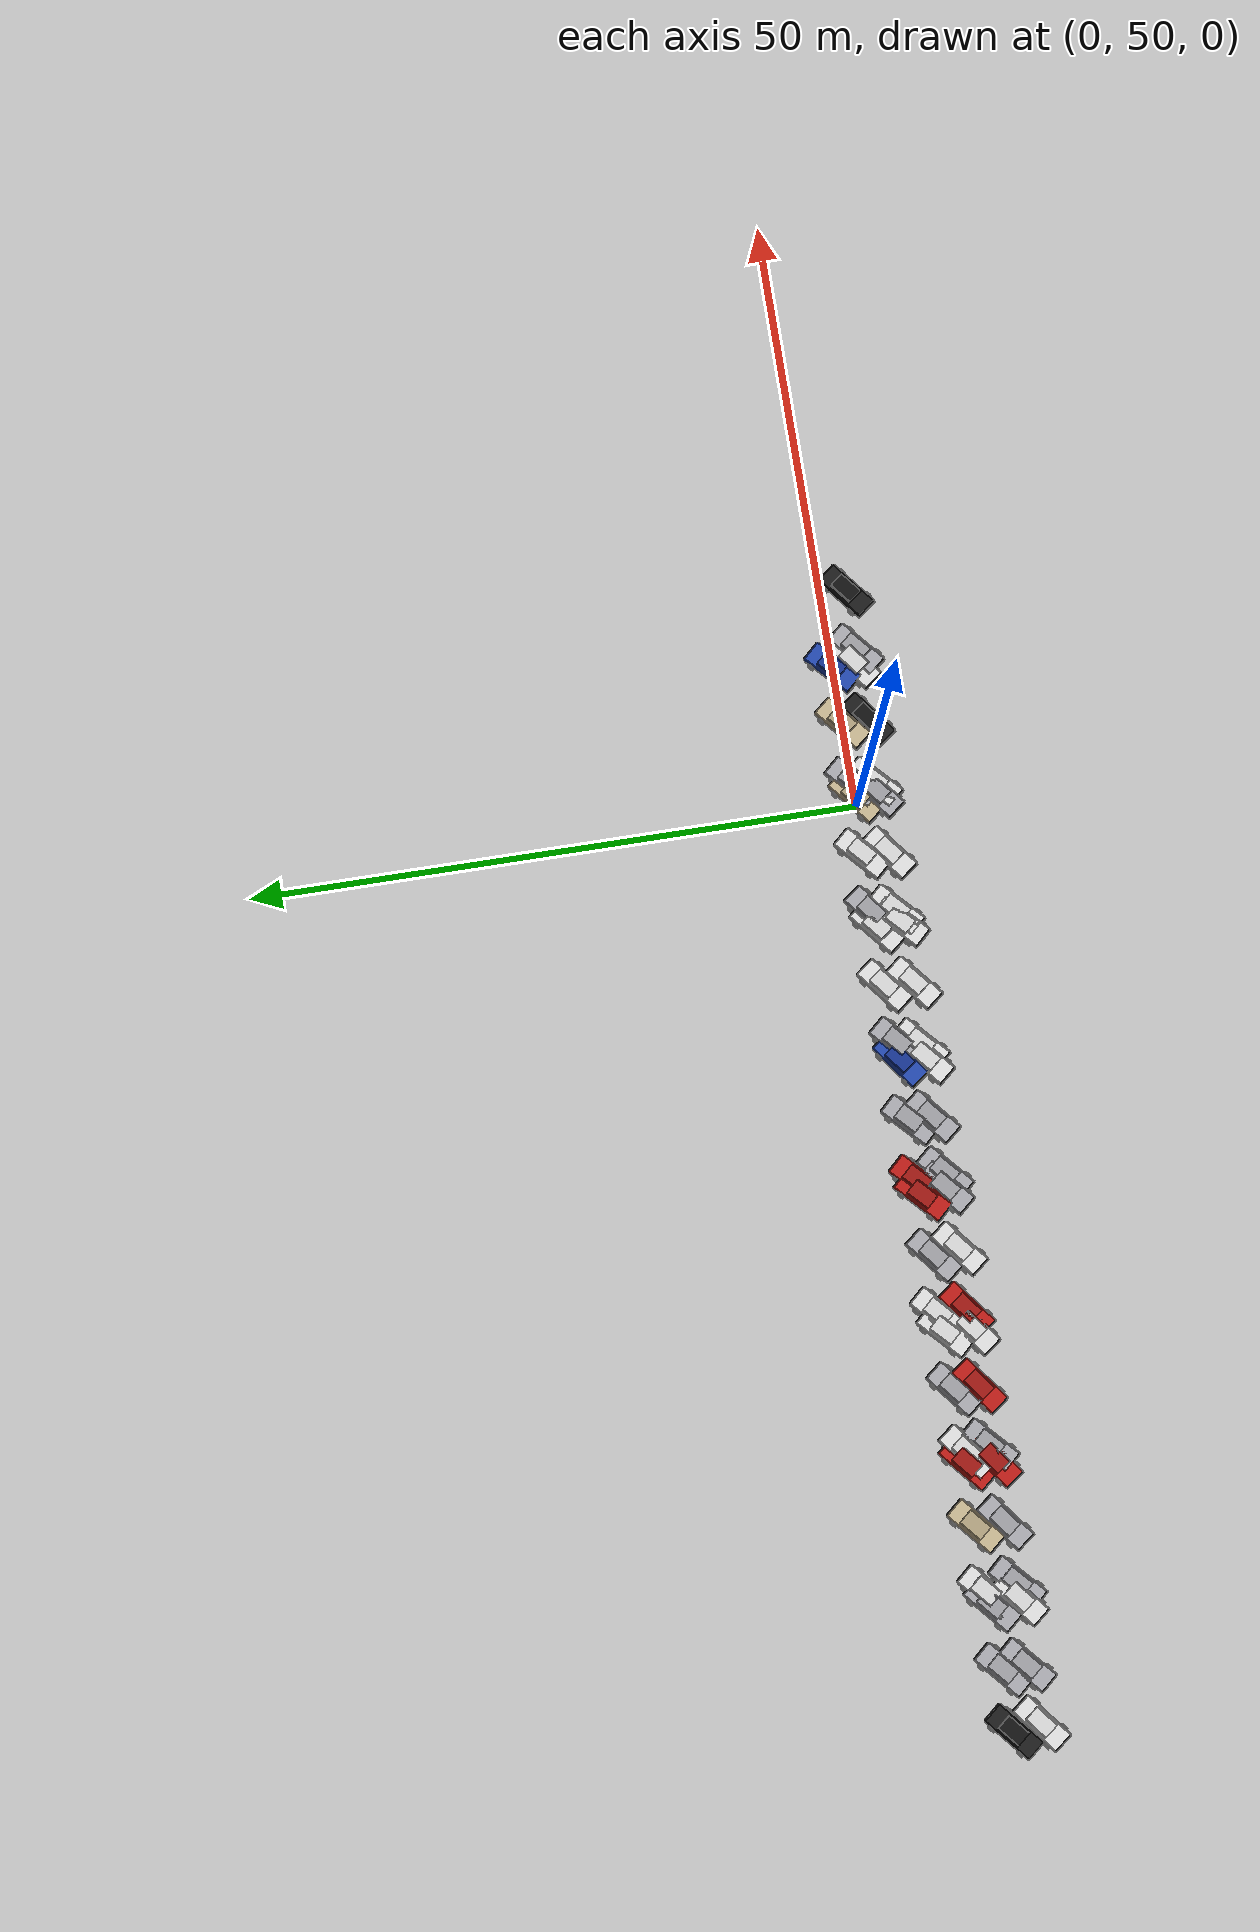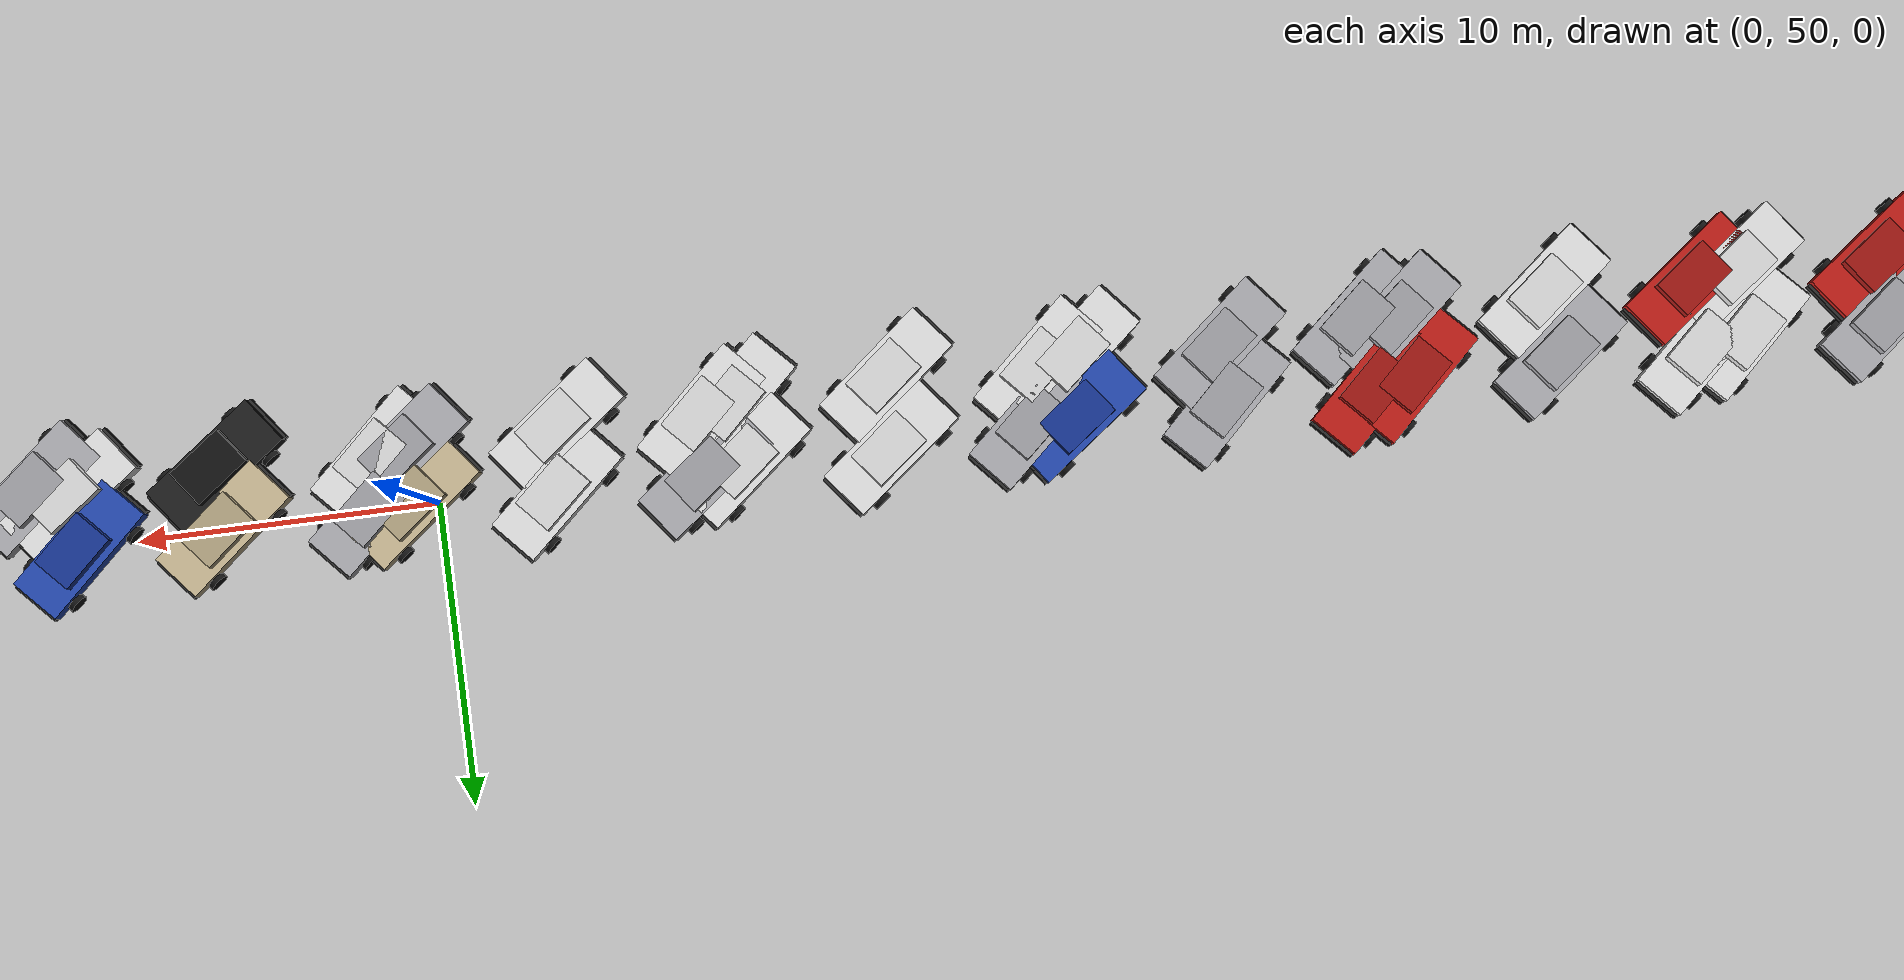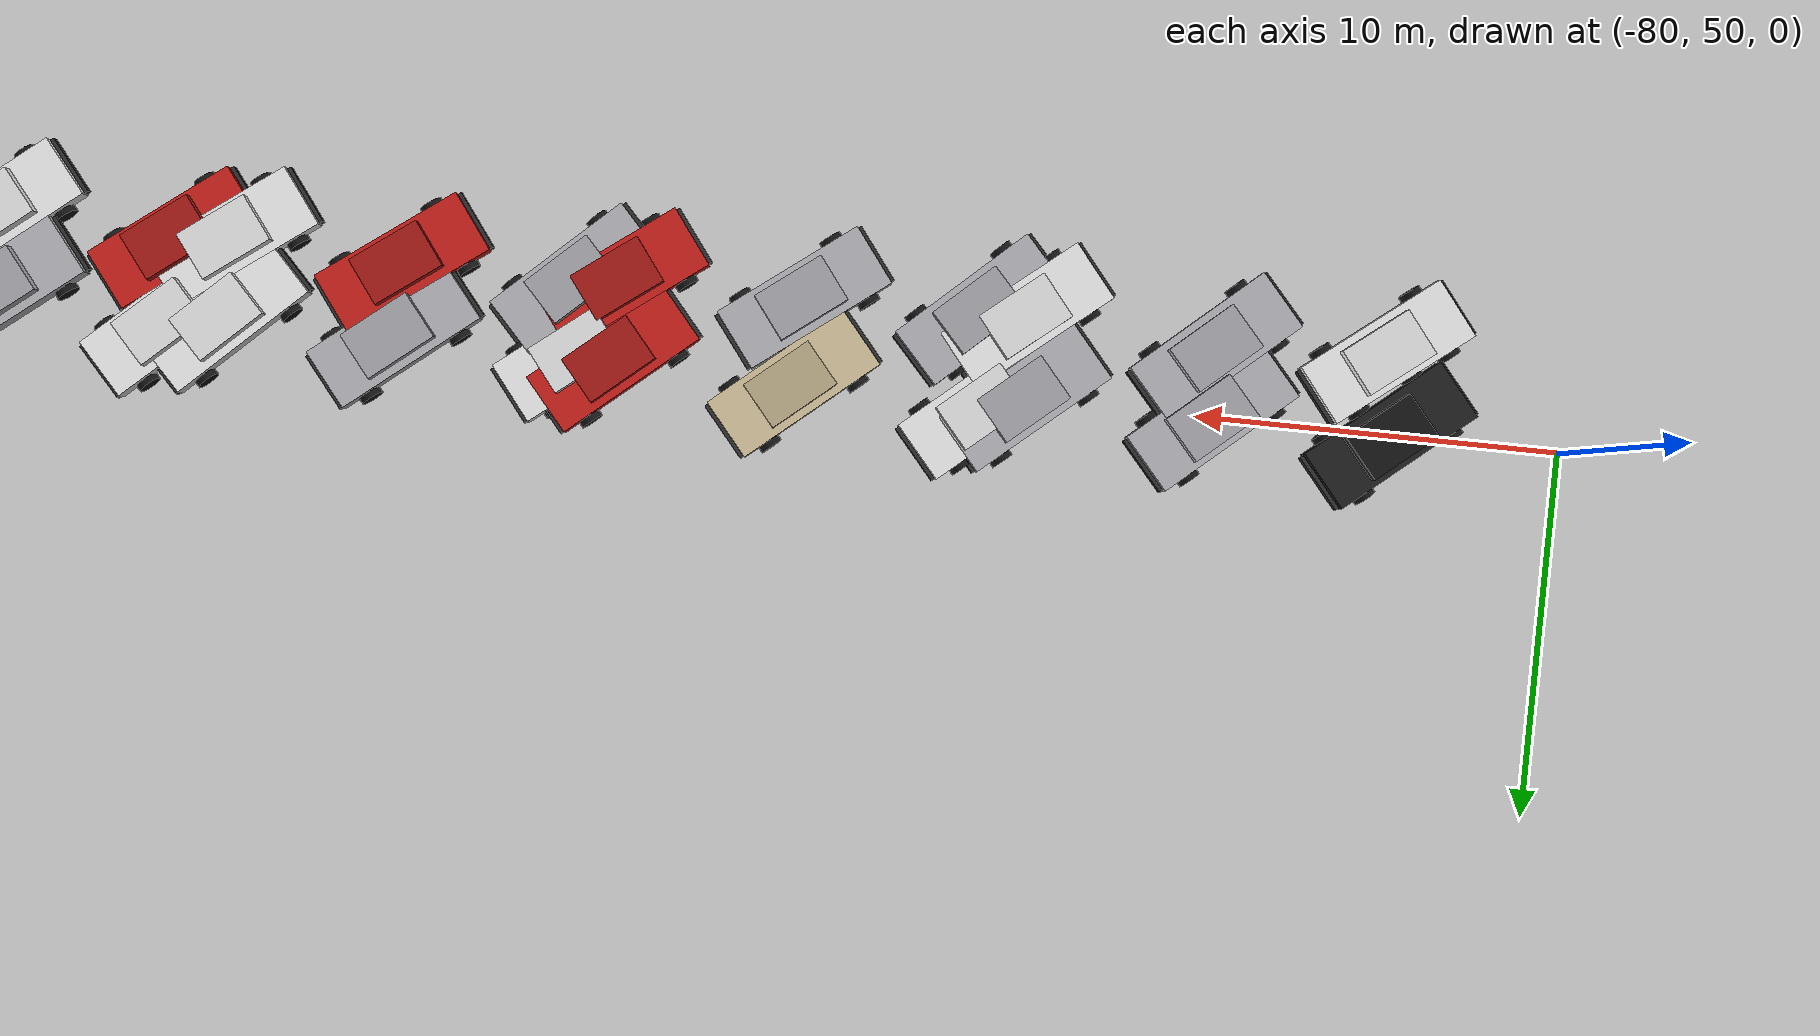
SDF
<?xml version="1.0" ?>
<sdf version="1.6">
  <world name="parking_lot">

    <!-- ═══════════════════ PHYSICS ═══════════════════ -->
    <physics type="ode">
      <real_time_update_rate>1000</real_time_update_rate>
      <max_step_size>0.001</max_step_size>
    </physics>

    <!-- ═══════════════════ SCENE ════════════════════ -->
    <scene>
      <sky>
        <clouds>
          <speed>12</speed>
        </clouds>
      </sky>
      <ambient>0.7 0.7 0.7 1</ambient>
      <background>0.55 0.55 0.58 1</background>
      <shadows>false</shadows>
    </scene>

    <!-- ═══════════════════ SUN ══════════════════════ -->
    <light name="sun" type="directional">
      <cast_shadows>false</cast_shadows>
      <pose>0 0 100 0 -0 0</pose>
      <diffuse>0.9 0.9 0.85 1</diffuse>
      <specular>0.3 0.3 0.3 1</specular>
      <direction>-0.3 0.2 -0.9</direction>
    </light>

    <!-- ═══════════════════ GROUND PLANE (bare asphalt) ══════════════════ -->
    <model name="ground_plane">
      <static>true</static>
      <link name="link">
        <collision name="collision">
          <geometry>
            <plane>
              <normal>0 0 1</normal>
              <size>400 300</size>
            </plane>
          </geometry>
          <surface>
            <friction><ode><mu>0.8</mu><mu2>0.8</mu2></ode></friction>
          </surface>
        </collision>
        <visual name="visual">
          <cast_shadows>false</cast_shadows>
          <geometry>
            <plane>
              <normal>0 0 1</normal>
              <size>400 300</size>
            </plane>
          </geometry>
          <material>
            <script>
              <uri>file://media/materials/scripts/gazebo.material</uri>
              <name>Gazebo/Grey</name>
            </script>
            <!-- Asphalt-grey colour override -->
            <ambient>0.28 0.28 0.27 1</ambient>
            <diffuse>0.32 0.32 0.30 1</diffuse>
            <specular>0.01 0.01 0.01 1</specular>
          </material>
        </visual>
      </link>
    </model>

    <model name="car_0000">
      <static>true</static>
      <pose>-74.930 47.763 0 0 0 0.6667</pose>

      <!-- Body -->
      <link name="body">
        <visual name="body_vis">
          <pose>0 0 0.55 0 0 0</pose>
          <geometry><box><size>4.45 1.80 0.55</size></box></geometry>
          <material>
            <ambient>0.15 0.15 0.15 1</ambient>
            <diffuse>0.92 0.92 0.92 1</diffuse>
            <specular>0.4 0.4 0.4 1</specular>
          </material>
        </visual>
        <!-- Cabin/roof -->
        <visual name="roof_vis">
          <pose>0.10 0 1.12 0 0 0</pose>
          <geometry><box><size>2.10 1.40 0.40</size></box></geometry>
          <material>
            <ambient>0.10 0.10 0.10 1</ambient>
            <diffuse>0.88 0.88 0.88 1</diffuse>
            <specular>0.5 0.5 0.5 1</specular>
          </material>
        </visual>
        <!-- Windscreen tint -->
        <visual name="glass_f">
          <pose>1.02 0 0.95 0 -0.45 0</pose>
          <geometry><box><size>0.05 1.35 0.38</size></box></geometry>
          <material><diffuse>0.50 0.60 0.70 0.6</diffuse></material>
        </visual>
        <!-- Front bumper -->
        <visual name="bumper_f">
          <pose>2.28 0 0.42 0 0 0</pose>
          <geometry><box><size>0.12 1.72 0.28</size></box></geometry>
          <material><diffuse>0.18 0.18 0.18 1</diffuse></material>
        </visual>
        <!-- Rear bumper -->
        <visual name="bumper_r">
          <pose>-2.28 0 0.42 0 0 0</pose>
          <geometry><box><size>0.12 1.72 0.28</size></box></geometry>
          <material><diffuse>0.18 0.18 0.18 1</diffuse></material>
        </visual>
        <!-- Wheels (4) -->
        <visual name="wfl">
          <pose>1.45 0.85 0.32 1.5708 0 0</pose>
          <geometry><cylinder><radius>0.32</radius><length>0.44</length></cylinder></geometry>
          <material><diffuse>0.08 0.08 0.08 1</diffuse></material>
        </visual>
        <visual name="wfr">
          <pose>1.45 -0.85 0.32 1.5708 0 0</pose>
          <geometry><cylinder><radius>0.32</radius><length>0.44</length></cylinder></geometry>
          <material><diffuse>0.08 0.08 0.08 1</diffuse></material>
        </visual>
        <visual name="wrl">
          <pose>-1.45 0.85 0.32 1.5708 0 0</pose>
          <geometry><cylinder><radius>0.32</radius><length>0.44</length></cylinder></geometry>
          <material><diffuse>0.08 0.08 0.08 1</diffuse></material>
        </visual>
        <visual name="wrr">
          <pose>-1.45 -0.85 0.32 1.5708 0 0</pose>
          <geometry><cylinder><radius>0.32</radius><length>0.44</length></cylinder></geometry>
          <material><diffuse>0.08 0.08 0.08 1</diffuse></material>
        </visual>
        <!-- Collision (simplified box) -->
        <collision name="col">
          <pose>0 0 0.55 0 0 0</pose>
          <geometry><box><size>4.45 1.80 1.30</size></box></geometry>
        </collision>
      </link>
    </model>
    <model name="car_0001">
      <static>true</static>
      <pose>-70.288 48.118 0 0 0 0.7228</pose>

      <!-- Body -->
      <link name="body">
        <visual name="body_vis">
          <pose>0 0 0.55 0 0 0</pose>
          <geometry><box><size>4.45 1.80 0.55</size></box></geometry>
          <material>
            <ambient>0.15 0.15 0.15 1</ambient>
            <diffuse>0.70 0.70 0.72 1</diffuse>
            <specular>0.4 0.4 0.4 1</specular>
          </material>
        </visual>
        <!-- Cabin/roof -->
        <visual name="roof_vis">
          <pose>0.10 0 1.12 0 0 0</pose>
          <geometry><box><size>2.10 1.40 0.40</size></box></geometry>
          <material>
            <ambient>0.10 0.10 0.10 1</ambient>
            <diffuse>0.65 0.65 0.67 1</diffuse>
            <specular>0.5 0.5 0.5 1</specular>
          </material>
        </visual>
        <!-- Windscreen tint -->
        <visual name="glass_f">
          <pose>1.02 0 0.95 0 -0.45 0</pose>
          <geometry><box><size>0.05 1.35 0.38</size></box></geometry>
          <material><diffuse>0.50 0.60 0.70 0.6</diffuse></material>
        </visual>
        <!-- Front bumper -->
        <visual name="bumper_f">
          <pose>2.28 0 0.42 0 0 0</pose>
          <geometry><box><size>0.12 1.72 0.28</size></box></geometry>
          <material><diffuse>0.18 0.18 0.18 1</diffuse></material>
        </visual>
        <!-- Rear bumper -->
        <visual name="bumper_r">
          <pose>-2.28 0 0.42 0 0 0</pose>
          <geometry><box><size>0.12 1.72 0.28</size></box></geometry>
          <material><diffuse>0.18 0.18 0.18 1</diffuse></material>
        </visual>
        <!-- Wheels (4) -->
        <visual name="wfl">
          <pose>1.45 0.85 0.32 1.5708 0 0</pose>
          <geometry><cylinder><radius>0.32</radius><length>0.44</length></cylinder></geometry>
          <material><diffuse>0.08 0.08 0.08 1</diffuse></material>
        </visual>
        <visual name="wfr">
          <pose>1.45 -0.85 0.32 1.5708 0 0</pose>
          <geometry><cylinder><radius>0.32</radius><length>0.44</length></cylinder></geometry>
          <material><diffuse>0.08 0.08 0.08 1</diffuse></material>
        </visual>
        <visual name="wrl">
          <pose>-1.45 0.85 0.32 1.5708 0 0</pose>
          <geometry><cylinder><radius>0.32</radius><length>0.44</length></cylinder></geometry>
          <material><diffuse>0.08 0.08 0.08 1</diffuse></material>
        </visual>
        <visual name="wrr">
          <pose>-1.45 -0.85 0.32 1.5708 0 0</pose>
          <geometry><cylinder><radius>0.32</radius><length>0.44</length></cylinder></geometry>
          <material><diffuse>0.08 0.08 0.08 1</diffuse></material>
        </visual>
        <!-- Collision (simplified box) -->
        <collision name="col">
          <pose>0 0 0.55 0 0 0</pose>
          <geometry><box><size>4.45 1.80 1.30</size></box></geometry>
        </collision>
      </link>
    </model>
    <model name="car_0002">
      <static>true</static>
      <pose>-65.104 47.793 0 0 0 0.6872</pose>

      <!-- Body -->
      <link name="body">
        <visual name="body_vis">
          <pose>0 0 0.55 0 0 0</pose>
          <geometry><box><size>4.45 1.80 0.55</size></box></geometry>
          <material>
            <ambient>0.15 0.15 0.15 1</ambient>
            <diffuse>0.92 0.92 0.92 1</diffuse>
            <specular>0.4 0.4 0.4 1</specular>
          </material>
        </visual>
        <!-- Cabin/roof -->
        <visual name="roof_vis">
          <pose>0.10 0 1.12 0 0 0</pose>
          <geometry><box><size>2.10 1.40 0.40</size></box></geometry>
          <material>
            <ambient>0.10 0.10 0.10 1</ambient>
            <diffuse>0.88 0.88 0.88 1</diffuse>
            <specular>0.5 0.5 0.5 1</specular>
          </material>
        </visual>
        <!-- Windscreen tint -->
        <visual name="glass_f">
          <pose>1.02 0 0.95 0 -0.45 0</pose>
          <geometry><box><size>0.05 1.35 0.38</size></box></geometry>
          <material><diffuse>0.50 0.60 0.70 0.6</diffuse></material>
        </visual>
        <!-- Front bumper -->
        <visual name="bumper_f">
          <pose>2.28 0 0.42 0 0 0</pose>
          <geometry><box><size>0.12 1.72 0.28</size></box></geometry>
          <material><diffuse>0.18 0.18 0.18 1</diffuse></material>
        </visual>
        <!-- Rear bumper -->
        <visual name="bumper_r">
          <pose>-2.28 0 0.42 0 0 0</pose>
          <geometry><box><size>0.12 1.72 0.28</size></box></geometry>
          <material><diffuse>0.18 0.18 0.18 1</diffuse></material>
        </visual>
        <!-- Wheels (4) -->
        <visual name="wfl">
          <pose>1.45 0.85 0.32 1.5708 0 0</pose>
          <geometry><cylinder><radius>0.32</radius><length>0.44</length></cylinder></geometry>
          <material><diffuse>0.08 0.08 0.08 1</diffuse></material>
        </visual>
        <visual name="wfr">
          <pose>1.45 -0.85 0.32 1.5708 0 0</pose>
          <geometry><cylinder><radius>0.32</radius><length>0.44</length></cylinder></geometry>
          <material><diffuse>0.08 0.08 0.08 1</diffuse></material>
        </visual>
        <visual name="wrl">
          <pose>-1.45 0.85 0.32 1.5708 0 0</pose>
          <geometry><cylinder><radius>0.32</radius><length>0.44</length></cylinder></geometry>
          <material><diffuse>0.08 0.08 0.08 1</diffuse></material>
        </visual>
        <visual name="wrr">
          <pose>-1.45 -0.85 0.32 1.5708 0 0</pose>
          <geometry><cylinder><radius>0.32</radius><length>0.44</length></cylinder></geometry>
          <material><diffuse>0.08 0.08 0.08 1</diffuse></material>
        </visual>
        <!-- Collision (simplified box) -->
        <collision name="col">
          <pose>0 0 0.55 0 0 0</pose>
          <geometry><box><size>4.45 1.80 1.30</size></box></geometry>
        </collision>
      </link>
    </model>
    <model name="car_0003">
      <static>true</static>
      <pose>-75.235 50.009 0 0 0 0.6989</pose>

      <!-- Body -->
      <link name="body">
        <visual name="body_vis">
          <pose>0 0 0.55 0 0 0</pose>
          <geometry><box><size>4.45 1.80 0.55</size></box></geometry>
          <material>
            <ambient>0.15 0.15 0.15 1</ambient>
            <diffuse>0.12 0.12 0.12 1</diffuse>
            <specular>0.4 0.4 0.4 1</specular>
          </material>
        </visual>
        <!-- Cabin/roof -->
        <visual name="roof_vis">
          <pose>0.10 0 1.12 0 0 0</pose>
          <geometry><box><size>2.10 1.40 0.40</size></box></geometry>
          <material>
            <ambient>0.10 0.10 0.10 1</ambient>
            <diffuse>0.08 0.08 0.08 1</diffuse>
            <specular>0.5 0.5 0.5 1</specular>
          </material>
        </visual>
        <!-- Windscreen tint -->
        <visual name="glass_f">
          <pose>1.02 0 0.95 0 -0.45 0</pose>
          <geometry><box><size>0.05 1.35 0.38</size></box></geometry>
          <material><diffuse>0.50 0.60 0.70 0.6</diffuse></material>
        </visual>
        <!-- Front bumper -->
        <visual name="bumper_f">
          <pose>2.28 0 0.42 0 0 0</pose>
          <geometry><box><size>0.12 1.72 0.28</size></box></geometry>
          <material><diffuse>0.18 0.18 0.18 1</diffuse></material>
        </visual>
        <!-- Rear bumper -->
        <visual name="bumper_r">
          <pose>-2.28 0 0.42 0 0 0</pose>
          <geometry><box><size>0.12 1.72 0.28</size></box></geometry>
          <material><diffuse>0.18 0.18 0.18 1</diffuse></material>
        </visual>
        <!-- Wheels (4) -->
        <visual name="wfl">
          <pose>1.45 0.85 0.32 1.5708 0 0</pose>
          <geometry><cylinder><radius>0.32</radius><length>0.44</length></cylinder></geometry>
          <material><diffuse>0.08 0.08 0.08 1</diffuse></material>
        </visual>
        <visual name="wfr">
          <pose>1.45 -0.85 0.32 1.5708 0 0</pose>
          <geometry><cylinder><radius>0.32</radius><length>0.44</length></cylinder></geometry>
          <material><diffuse>0.08 0.08 0.08 1</diffuse></material>
        </visual>
        <visual name="wrl">
          <pose>-1.45 0.85 0.32 1.5708 0 0</pose>
          <geometry><cylinder><radius>0.32</radius><length>0.44</length></cylinder></geometry>
          <material><diffuse>0.08 0.08 0.08 1</diffuse></material>
        </visual>
        <visual name="wrr">
          <pose>-1.45 -0.85 0.32 1.5708 0 0</pose>
          <geometry><cylinder><radius>0.32</radius><length>0.44</length></cylinder></geometry>
          <material><diffuse>0.08 0.08 0.08 1</diffuse></material>
        </visual>
        <!-- Collision (simplified box) -->
        <collision name="col">
          <pose>0 0 0.55 0 0 0</pose>
          <geometry><box><size>4.45 1.80 1.30</size></box></geometry>
        </collision>
      </link>
    </model>
    <model name="car_0004">
      <static>true</static>
      <pose>-70.387 49.999 0 0 0 0.7191</pose>

      <!-- Body -->
      <link name="body">
        <visual name="body_vis">
          <pose>0 0 0.55 0 0 0</pose>
          <geometry><box><size>4.45 1.80 0.55</size></box></geometry>
          <material>
            <ambient>0.15 0.15 0.15 1</ambient>
            <diffuse>0.70 0.70 0.72 1</diffuse>
            <specular>0.4 0.4 0.4 1</specular>
          </material>
        </visual>
        <!-- Cabin/roof -->
        <visual name="roof_vis">
          <pose>0.10 0 1.12 0 0 0</pose>
          <geometry><box><size>2.10 1.40 0.40</size></box></geometry>
          <material>
            <ambient>0.10 0.10 0.10 1</ambient>
            <diffuse>0.65 0.65 0.67 1</diffuse>
            <specular>0.5 0.5 0.5 1</specular>
          </material>
        </visual>
        <!-- Windscreen tint -->
        <visual name="glass_f">
          <pose>1.02 0 0.95 0 -0.45 0</pose>
          <geometry><box><size>0.05 1.35 0.38</size></box></geometry>
          <material><diffuse>0.50 0.60 0.70 0.6</diffuse></material>
        </visual>
        <!-- Front bumper -->
        <visual name="bumper_f">
          <pose>2.28 0 0.42 0 0 0</pose>
          <geometry><box><size>0.12 1.72 0.28</size></box></geometry>
          <material><diffuse>0.18 0.18 0.18 1</diffuse></material>
        </visual>
        <!-- Rear bumper -->
        <visual name="bumper_r">
          <pose>-2.28 0 0.42 0 0 0</pose>
          <geometry><box><size>0.12 1.72 0.28</size></box></geometry>
          <material><diffuse>0.18 0.18 0.18 1</diffuse></material>
        </visual>
        <!-- Wheels (4) -->
        <visual name="wfl">
          <pose>1.45 0.85 0.32 1.5708 0 0</pose>
          <geometry><cylinder><radius>0.32</radius><length>0.44</length></cylinder></geometry>
          <material><diffuse>0.08 0.08 0.08 1</diffuse></material>
        </visual>
        <visual name="wfr">
          <pose>1.45 -0.85 0.32 1.5708 0 0</pose>
          <geometry><cylinder><radius>0.32</radius><length>0.44</length></cylinder></geometry>
          <material><diffuse>0.08 0.08 0.08 1</diffuse></material>
        </visual>
        <visual name="wrl">
          <pose>-1.45 0.85 0.32 1.5708 0 0</pose>
          <geometry><cylinder><radius>0.32</radius><length>0.44</length></cylinder></geometry>
          <material><diffuse>0.08 0.08 0.08 1</diffuse></material>
        </visual>
        <visual name="wrr">
          <pose>-1.45 -0.85 0.32 1.5708 0 0</pose>
          <geometry><cylinder><radius>0.32</radius><length>0.44</length></cylinder></geometry>
          <material><diffuse>0.08 0.08 0.08 1</diffuse></material>
        </visual>
        <!-- Collision (simplified box) -->
        <collision name="col">
          <pose>0 0 0.55 0 0 0</pose>
          <geometry><box><size>4.45 1.80 1.30</size></box></geometry>
        </collision>
      </link>
    </model>
    <model name="car_0005">
      <static>true</static>
      <pose>-65.278 50.010 0 0 0 0.7106</pose>

      <!-- Body -->
      <link name="body">
        <visual name="body_vis">
          <pose>0 0 0.55 0 0 0</pose>
          <geometry><box><size>4.45 1.80 0.55</size></box></geometry>
          <material>
            <ambient>0.15 0.15 0.15 1</ambient>
            <diffuse>0.70 0.70 0.72 1</diffuse>
            <specular>0.4 0.4 0.4 1</specular>
          </material>
        </visual>
        <!-- Cabin/roof -->
        <visual name="roof_vis">
          <pose>0.10 0 1.12 0 0 0</pose>
          <geometry><box><size>2.10 1.40 0.40</size></box></geometry>
          <material>
            <ambient>0.10 0.10 0.10 1</ambient>
            <diffuse>0.65 0.65 0.67 1</diffuse>
            <specular>0.5 0.5 0.5 1</specular>
          </material>
        </visual>
        <!-- Windscreen tint -->
        <visual name="glass_f">
          <pose>1.02 0 0.95 0 -0.45 0</pose>
          <geometry><box><size>0.05 1.35 0.38</size></box></geometry>
          <material><diffuse>0.50 0.60 0.70 0.6</diffuse></material>
        </visual>
        <!-- Front bumper -->
        <visual name="bumper_f">
          <pose>2.28 0 0.42 0 0 0</pose>
          <geometry><box><size>0.12 1.72 0.28</size></box></geometry>
          <material><diffuse>0.18 0.18 0.18 1</diffuse></material>
        </visual>
        <!-- Rear bumper -->
        <visual name="bumper_r">
          <pose>-2.28 0 0.42 0 0 0</pose>
          <geometry><box><size>0.12 1.72 0.28</size></box></geometry>
          <material><diffuse>0.18 0.18 0.18 1</diffuse></material>
        </visual>
        <!-- Wheels (4) -->
        <visual name="wfl">
          <pose>1.45 0.85 0.32 1.5708 0 0</pose>
          <geometry><cylinder><radius>0.32</radius><length>0.44</length></cylinder></geometry>
          <material><diffuse>0.08 0.08 0.08 1</diffuse></material>
        </visual>
        <visual name="wfr">
          <pose>1.45 -0.85 0.32 1.5708 0 0</pose>
          <geometry><cylinder><radius>0.32</radius><length>0.44</length></cylinder></geometry>
          <material><diffuse>0.08 0.08 0.08 1</diffuse></material>
        </visual>
        <visual name="wrl">
          <pose>-1.45 0.85 0.32 1.5708 0 0</pose>
          <geometry><cylinder><radius>0.32</radius><length>0.44</length></cylinder></geometry>
          <material><diffuse>0.08 0.08 0.08 1</diffuse></material>
        </visual>
        <visual name="wrr">
          <pose>-1.45 -0.85 0.32 1.5708 0 0</pose>
          <geometry><cylinder><radius>0.32</radius><length>0.44</length></cylinder></geometry>
          <material><diffuse>0.08 0.08 0.08 1</diffuse></material>
        </visual>
        <!-- Collision (simplified box) -->
        <collision name="col">
          <pose>0 0 0.55 0 0 0</pose>
          <geometry><box><size>4.45 1.80 1.30</size></box></geometry>
        </collision>
      </link>
    </model>
    <model name="car_0006">
      <static>true</static>
      <pose>-63.845 47.753 0 0 0 0.7408</pose>

      <!-- Body -->
      <link name="body">
        <visual name="body_vis">
          <pose>0 0 0.55 0 0 0</pose>
          <geometry><box><size>4.45 1.80 0.55</size></box></geometry>
          <material>
            <ambient>0.15 0.15 0.15 1</ambient>
            <diffuse>0.70 0.70 0.72 1</diffuse>
            <specular>0.4 0.4 0.4 1</specular>
          </material>
        </visual>
        <!-- Cabin/roof -->
        <visual name="roof_vis">
          <pose>0.10 0 1.12 0 0 0</pose>
          <geometry><box><size>2.10 1.40 0.40</size></box></geometry>
          <material>
            <ambient>0.10 0.10 0.10 1</ambient>
            <diffuse>0.65 0.65 0.67 1</diffuse>
            <specular>0.5 0.5 0.5 1</specular>
          </material>
        </visual>
        <!-- Windscreen tint -->
        <visual name="glass_f">
          <pose>1.02 0 0.95 0 -0.45 0</pose>
          <geometry><box><size>0.05 1.35 0.38</size></box></geometry>
          <material><diffuse>0.50 0.60 0.70 0.6</diffuse></material>
        </visual>
        <!-- Front bumper -->
        <visual name="bumper_f">
          <pose>2.28 0 0.42 0 0 0</pose>
          <geometry><box><size>0.12 1.72 0.28</size></box></geometry>
          <material><diffuse>0.18 0.18 0.18 1</diffuse></material>
        </visual>
        <!-- Rear bumper -->
        <visual name="bumper_r">
          <pose>-2.28 0 0.42 0 0 0</pose>
          <geometry><box><size>0.12 1.72 0.28</size></box></geometry>
          <material><diffuse>0.18 0.18 0.18 1</diffuse></material>
        </visual>
        <!-- Wheels (4) -->
        <visual name="wfl">
          <pose>1.45 0.85 0.32 1.5708 0 0</pose>
          <geometry><cylinder><radius>0.32</radius><length>0.44</length></cylinder></geometry>
          <material><diffuse>0.08 0.08 0.08 1</diffuse></material>
        </visual>
        <visual name="wfr">
          <pose>1.45 -0.85 0.32 1.5708 0 0</pose>
          <geometry><cylinder><radius>0.32</radius><length>0.44</length></cylinder></geometry>
          <material><diffuse>0.08 0.08 0.08 1</diffuse></material>
        </visual>
        <visual name="wrl">
          <pose>-1.45 0.85 0.32 1.5708 0 0</pose>
          <geometry><cylinder><radius>0.32</radius><length>0.44</length></cylinder></geometry>
          <material><diffuse>0.08 0.08 0.08 1</diffuse></material>
        </visual>
        <visual name="wrr">
          <pose>-1.45 -0.85 0.32 1.5708 0 0</pose>
          <geometry><cylinder><radius>0.32</radius><length>0.44</length></cylinder></geometry>
          <material><diffuse>0.08 0.08 0.08 1</diffuse></material>
        </visual>
        <!-- Collision (simplified box) -->
        <collision name="col">
          <pose>0 0 0.55 0 0 0</pose>
          <geometry><box><size>4.45 1.80 1.30</size></box></geometry>
        </collision>
      </link>
    </model>
    <model name="car_0007">
      <static>true</static>
      <pose>-59.051 47.920 0 0 0 0.6500</pose>

      <!-- Body -->
      <link name="body">
        <visual name="body_vis">
          <pose>0 0 0.55 0 0 0</pose>
          <geometry><box><size>4.45 1.80 0.55</size></box></geometry>
          <material>
            <ambient>0.15 0.15 0.15 1</ambient>
            <diffuse>0.70 0.70 0.72 1</diffuse>
            <specular>0.4 0.4 0.4 1</specular>
          </material>
        </visual>
        <!-- Cabin/roof -->
        <visual name="roof_vis">
          <pose>0.10 0 1.12 0 0 0</pose>
          <geometry><box><size>2.10 1.40 0.40</size></box></geometry>
          <material>
            <ambient>0.10 0.10 0.10 1</ambient>
            <diffuse>0.65 0.65 0.67 1</diffuse>
            <specular>0.5 0.5 0.5 1</specular>
          </material>
        </visual>
        <!-- Windscreen tint -->
        <visual name="glass_f">
          <pose>1.02 0 0.95 0 -0.45 0</pose>
          <geometry><box><size>0.05 1.35 0.38</size></box></geometry>
          <material><diffuse>0.50 0.60 0.70 0.6</diffuse></material>
        </visual>
        <!-- Front bumper -->
        <visual name="bumper_f">
          <pose>2.28 0 0.42 0 0 0</pose>
          <geometry><box><size>0.12 1.72 0.28</size></box></geometry>
          <material><diffuse>0.18 0.18 0.18 1</diffuse></material>
        </visual>
        <!-- Rear bumper -->
        <visual name="bumper_r">
          <pose>-2.28 0 0.42 0 0 0</pose>
          <geometry><box><size>0.12 1.72 0.28</size></box></geometry>
          <material><diffuse>0.18 0.18 0.18 1</diffuse></material>
        </visual>
        <!-- Wheels (4) -->
        <visual name="wfl">
          <pose>1.45 0.85 0.32 1.5708 0 0</pose>
          <geometry><cylinder><radius>0.32</radius><length>0.44</length></cylinder></geometry>
          <material><diffuse>0.08 0.08 0.08 1</diffuse></material>
        </visual>
        <visual name="wfr">
          <pose>1.45 -0.85 0.32 1.5708 0 0</pose>
          <geometry><cylinder><radius>0.32</radius><length>0.44</length></cylinder></geometry>
          <material><diffuse>0.08 0.08 0.08 1</diffuse></material>
        </visual>
        <visual name="wrl">
          <pose>-1.45 0.85 0.32 1.5708 0 0</pose>
          <geometry><cylinder><radius>0.32</radius><length>0.44</length></cylinder></geometry>
          <material><diffuse>0.08 0.08 0.08 1</diffuse></material>
        </visual>
        <visual name="wrr">
          <pose>-1.45 -0.85 0.32 1.5708 0 0</pose>
          <geometry><cylinder><radius>0.32</radius><length>0.44</length></cylinder></geometry>
          <material><diffuse>0.08 0.08 0.08 1</diffuse></material>
        </visual>
        <!-- Collision (simplified box) -->
        <collision name="col">
          <pose>0 0 0.55 0 0 0</pose>
          <geometry><box><size>4.45 1.80 1.30</size></box></geometry>
        </collision>
      </link>
    </model>
    <model name="car_0008">
      <static>true</static>
      <pose>-54.071 47.918 0 0 0 0.6413</pose>

      <!-- Body -->
      <link name="body">
        <visual name="body_vis">
          <pose>0 0 0.55 0 0 0</pose>
          <geometry><box><size>4.45 1.80 0.55</size></box></geometry>
          <material>
            <ambient>0.15 0.15 0.15 1</ambient>
            <diffuse>0.78 0.12 0.10 1</diffuse>
            <specular>0.4 0.4 0.4 1</specular>
          </material>
        </visual>
        <!-- Cabin/roof -->
        <visual name="roof_vis">
          <pose>0.10 0 1.12 0 0 0</pose>
          <geometry><box><size>2.10 1.40 0.40</size></box></geometry>
          <material>
            <ambient>0.10 0.10 0.10 1</ambient>
            <diffuse>0.65 0.10 0.08 1</diffuse>
            <specular>0.5 0.5 0.5 1</specular>
          </material>
        </visual>
        <!-- Windscreen tint -->
        <visual name="glass_f">
          <pose>1.02 0 0.95 0 -0.45 0</pose>
          <geometry><box><size>0.05 1.35 0.38</size></box></geometry>
          <material><diffuse>0.50 0.60 0.70 0.6</diffuse></material>
        </visual>
        <!-- Front bumper -->
        <visual name="bumper_f">
          <pose>2.28 0 0.42 0 0 0</pose>
          <geometry><box><size>0.12 1.72 0.28</size></box></geometry>
          <material><diffuse>0.18 0.18 0.18 1</diffuse></material>
        </visual>
        <!-- Rear bumper -->
        <visual name="bumper_r">
          <pose>-2.28 0 0.42 0 0 0</pose>
          <geometry><box><size>0.12 1.72 0.28</size></box></geometry>
          <material><diffuse>0.18 0.18 0.18 1</diffuse></material>
        </visual>
        <!-- Wheels (4) -->
        <visual name="wfl">
          <pose>1.45 0.85 0.32 1.5708 0 0</pose>
          <geometry><cylinder><radius>0.32</radius><length>0.44</length></cylinder></geometry>
          <material><diffuse>0.08 0.08 0.08 1</diffuse></material>
        </visual>
        <visual name="wfr">
          <pose>1.45 -0.85 0.32 1.5708 0 0</pose>
          <geometry><cylinder><radius>0.32</radius><length>0.44</length></cylinder></geometry>
          <material><diffuse>0.08 0.08 0.08 1</diffuse></material>
        </visual>
        <visual name="wrl">
          <pose>-1.45 0.85 0.32 1.5708 0 0</pose>
          <geometry><cylinder><radius>0.32</radius><length>0.44</length></cylinder></geometry>
          <material><diffuse>0.08 0.08 0.08 1</diffuse></material>
        </visual>
        <visual name="wrr">
          <pose>-1.45 -0.85 0.32 1.5708 0 0</pose>
          <geometry><cylinder><radius>0.32</radius><length>0.44</length></cylinder></geometry>
          <material><diffuse>0.08 0.08 0.08 1</diffuse></material>
        </visual>
        <!-- Collision (simplified box) -->
        <collision name="col">
          <pose>0 0 0.55 0 0 0</pose>
          <geometry><box><size>4.45 1.80 1.30</size></box></geometry>
        </collision>
      </link>
    </model>
    <model name="car_0009">
      <static>true</static>
      <pose>-64.202 50.324 0 0 0 0.7126</pose>

      <!-- Body -->
      <link name="body">
        <visual name="body_vis">
          <pose>0 0 0.55 0 0 0</pose>
          <geometry><box><size>4.45 1.80 0.55</size></box></geometry>
          <material>
            <ambient>0.15 0.15 0.15 1</ambient>
            <diffuse>0.92 0.92 0.92 1</diffuse>
            <specular>0.4 0.4 0.4 1</specular>
          </material>
        </visual>
        <!-- Cabin/roof -->
        <visual name="roof_vis">
          <pose>0.10 0 1.12 0 0 0</pose>
          <geometry><box><size>2.10 1.40 0.40</size></box></geometry>
          <material>
            <ambient>0.10 0.10 0.10 1</ambient>
            <diffuse>0.88 0.88 0.88 1</diffuse>
            <specular>0.5 0.5 0.5 1</specular>
          </material>
        </visual>
        <!-- Windscreen tint -->
        <visual name="glass_f">
          <pose>1.02 0 0.95 0 -0.45 0</pose>
          <geometry><box><size>0.05 1.35 0.38</size></box></geometry>
          <material><diffuse>0.50 0.60 0.70 0.6</diffuse></material>
        </visual>
        <!-- Front bumper -->
        <visual name="bumper_f">
          <pose>2.28 0 0.42 0 0 0</pose>
          <geometry><box><size>0.12 1.72 0.28</size></box></geometry>
          <material><diffuse>0.18 0.18 0.18 1</diffuse></material>
        </visual>
        <!-- Rear bumper -->
        <visual name="bumper_r">
          <pose>-2.28 0 0.42 0 0 0</pose>
          <geometry><box><size>0.12 1.72 0.28</size></box></geometry>
          <material><diffuse>0.18 0.18 0.18 1</diffuse></material>
        </visual>
        <!-- Wheels (4) -->
        <visual name="wfl">
          <pose>1.45 0.85 0.32 1.5708 0 0</pose>
          <geometry><cylinder><radius>0.32</radius><length>0.44</length></cylinder></geometry>
          <material><diffuse>0.08 0.08 0.08 1</diffuse></material>
        </visual>
        <visual name="wfr">
          <pose>1.45 -0.85 0.32 1.5708 0 0</pose>
          <geometry><cylinder><radius>0.32</radius><length>0.44</length></cylinder></geometry>
          <material><diffuse>0.08 0.08 0.08 1</diffuse></material>
        </visual>
        <visual name="wrl">
          <pose>-1.45 0.85 0.32 1.5708 0 0</pose>
          <geometry><cylinder><radius>0.32</radius><length>0.44</length></cylinder></geometry>
          <material><diffuse>0.08 0.08 0.08 1</diffuse></material>
        </visual>
        <visual name="wrr">
          <pose>-1.45 -0.85 0.32 1.5708 0 0</pose>
          <geometry><cylinder><radius>0.32</radius><length>0.44</length></cylinder></geometry>
          <material><diffuse>0.08 0.08 0.08 1</diffuse></material>
        </visual>
        <!-- Collision (simplified box) -->
        <collision name="col">
          <pose>0 0 0.55 0 0 0</pose>
          <geometry><box><size>4.45 1.80 1.30</size></box></geometry>
        </collision>
      </link>
    </model>
    <model name="car_0010">
      <static>true</static>
      <pose>-58.996 50.265 0 0 0 0.7032</pose>

      <!-- Body -->
      <link name="body">
        <visual name="body_vis">
          <pose>0 0 0.55 0 0 0</pose>
          <geometry><box><size>4.45 1.80 0.55</size></box></geometry>
          <material>
            <ambient>0.15 0.15 0.15 1</ambient>
            <diffuse>0.82 0.75 0.60 1</diffuse>
            <specular>0.4 0.4 0.4 1</specular>
          </material>
        </visual>
        <!-- Cabin/roof -->
        <visual name="roof_vis">
          <pose>0.10 0 1.12 0 0 0</pose>
          <geometry><box><size>2.10 1.40 0.40</size></box></geometry>
          <material>
            <ambient>0.10 0.10 0.10 1</ambient>
            <diffuse>0.72 0.66 0.52 1</diffuse>
            <specular>0.5 0.5 0.5 1</specular>
          </material>
        </visual>
        <!-- Windscreen tint -->
        <visual name="glass_f">
          <pose>1.02 0 0.95 0 -0.45 0</pose>
          <geometry><box><size>0.05 1.35 0.38</size></box></geometry>
          <material><diffuse>0.50 0.60 0.70 0.6</diffuse></material>
        </visual>
        <!-- Front bumper -->
        <visual name="bumper_f">
          <pose>2.28 0 0.42 0 0 0</pose>
          <geometry><box><size>0.12 1.72 0.28</size></box></geometry>
          <material><diffuse>0.18 0.18 0.18 1</diffuse></material>
        </visual>
        <!-- Rear bumper -->
        <visual name="bumper_r">
          <pose>-2.28 0 0.42 0 0 0</pose>
          <geometry><box><size>0.12 1.72 0.28</size></box></geometry>
          <material><diffuse>0.18 0.18 0.18 1</diffuse></material>
        </visual>
        <!-- Wheels (4) -->
        <visual name="wfl">
          <pose>1.45 0.85 0.32 1.5708 0 0</pose>
          <geometry><cylinder><radius>0.32</radius><length>0.44</length></cylinder></geometry>
          <material><diffuse>0.08 0.08 0.08 1</diffuse></material>
        </visual>
        <visual name="wfr">
          <pose>1.45 -0.85 0.32 1.5708 0 0</pose>
          <geometry><cylinder><radius>0.32</radius><length>0.44</length></cylinder></geometry>
          <material><diffuse>0.08 0.08 0.08 1</diffuse></material>
        </visual>
        <visual name="wrl">
          <pose>-1.45 0.85 0.32 1.5708 0 0</pose>
          <geometry><cylinder><radius>0.32</radius><length>0.44</length></cylinder></geometry>
          <material><diffuse>0.08 0.08 0.08 1</diffuse></material>
        </visual>
        <visual name="wrr">
          <pose>-1.45 -0.85 0.32 1.5708 0 0</pose>
          <geometry><cylinder><radius>0.32</radius><length>0.44</length></cylinder></geometry>
          <material><diffuse>0.08 0.08 0.08 1</diffuse></material>
        </visual>
        <!-- Collision (simplified box) -->
        <collision name="col">
          <pose>0 0 0.55 0 0 0</pose>
          <geometry><box><size>4.45 1.80 1.30</size></box></geometry>
        </collision>
      </link>
    </model>
    <model name="car_0011">
      <static>true</static>
      <pose>-54.063 50.089 0 0 0 0.7054</pose>

      <!-- Body -->
      <link name="body">
        <visual name="body_vis">
          <pose>0 0 0.55 0 0 0</pose>
          <geometry><box><size>4.45 1.80 0.55</size></box></geometry>
          <material>
            <ambient>0.15 0.15 0.15 1</ambient>
            <diffuse>0.78 0.12 0.10 1</diffuse>
            <specular>0.4 0.4 0.4 1</specular>
          </material>
        </visual>
        <!-- Cabin/roof -->
        <visual name="roof_vis">
          <pose>0.10 0 1.12 0 0 0</pose>
          <geometry><box><size>2.10 1.40 0.40</size></box></geometry>
          <material>
            <ambient>0.10 0.10 0.10 1</ambient>
            <diffuse>0.65 0.10 0.08 1</diffuse>
            <specular>0.5 0.5 0.5 1</specular>
          </material>
        </visual>
        <!-- Windscreen tint -->
        <visual name="glass_f">
          <pose>1.02 0 0.95 0 -0.45 0</pose>
          <geometry><box><size>0.05 1.35 0.38</size></box></geometry>
          <material><diffuse>0.50 0.60 0.70 0.6</diffuse></material>
        </visual>
        <!-- Front bumper -->
        <visual name="bumper_f">
          <pose>2.28 0 0.42 0 0 0</pose>
          <geometry><box><size>0.12 1.72 0.28</size></box></geometry>
          <material><diffuse>0.18 0.18 0.18 1</diffuse></material>
        </visual>
        <!-- Rear bumper -->
        <visual name="bumper_r">
          <pose>-2.28 0 0.42 0 0 0</pose>
          <geometry><box><size>0.12 1.72 0.28</size></box></geometry>
          <material><diffuse>0.18 0.18 0.18 1</diffuse></material>
        </visual>
        <!-- Wheels (4) -->
        <visual name="wfl">
          <pose>1.45 0.85 0.32 1.5708 0 0</pose>
          <geometry><cylinder><radius>0.32</radius><length>0.44</length></cylinder></geometry>
          <material><diffuse>0.08 0.08 0.08 1</diffuse></material>
        </visual>
        <visual name="wfr">
          <pose>1.45 -0.85 0.32 1.5708 0 0</pose>
          <geometry><cylinder><radius>0.32</radius><length>0.44</length></cylinder></geometry>
          <material><diffuse>0.08 0.08 0.08 1</diffuse></material>
        </visual>
        <visual name="wrl">
          <pose>-1.45 0.85 0.32 1.5708 0 0</pose>
          <geometry><cylinder><radius>0.32</radius><length>0.44</length></cylinder></geometry>
          <material><diffuse>0.08 0.08 0.08 1</diffuse></material>
        </visual>
        <visual name="wrr">
          <pose>-1.45 -0.85 0.32 1.5708 0 0</pose>
          <geometry><cylinder><radius>0.32</radius><length>0.44</length></cylinder></geometry>
          <material><diffuse>0.08 0.08 0.08 1</diffuse></material>
        </visual>
        <!-- Collision (simplified box) -->
        <collision name="col">
          <pose>0 0 0.55 0 0 0</pose>
          <geometry><box><size>4.45 1.80 1.30</size></box></geometry>
        </collision>
      </link>
    </model>
    <model name="car_0012">
      <static>true</static>
      <pose>-52.835 48.059 0 0 0 0.7486</pose>

      <!-- Body -->
      <link name="body">
        <visual name="body_vis">
          <pose>0 0 0.55 0 0 0</pose>
          <geometry><box><size>4.45 1.80 0.55</size></box></geometry>
          <material>
            <ambient>0.15 0.15 0.15 1</ambient>
            <diffuse>0.70 0.70 0.72 1</diffuse>
            <specular>0.4 0.4 0.4 1</specular>
          </material>
        </visual>
        <!-- Cabin/roof -->
        <visual name="roof_vis">
          <pose>0.10 0 1.12 0 0 0</pose>
          <geometry><box><size>2.10 1.40 0.40</size></box></geometry>
          <material>
            <ambient>0.10 0.10 0.10 1</ambient>
            <diffuse>0.65 0.65 0.67 1</diffuse>
            <specular>0.5 0.5 0.5 1</specular>
          </material>
        </visual>
        <!-- Windscreen tint -->
        <visual name="glass_f">
          <pose>1.02 0 0.95 0 -0.45 0</pose>
          <geometry><box><size>0.05 1.35 0.38</size></box></geometry>
          <material><diffuse>0.50 0.60 0.70 0.6</diffuse></material>
        </visual>
        <!-- Front bumper -->
        <visual name="bumper_f">
          <pose>2.28 0 0.42 0 0 0</pose>
          <geometry><box><size>0.12 1.72 0.28</size></box></geometry>
          <material><diffuse>0.18 0.18 0.18 1</diffuse></material>
        </visual>
        <!-- Rear bumper -->
        <visual name="bumper_r">
          <pose>-2.28 0 0.42 0 0 0</pose>
          <geometry><box><size>0.12 1.72 0.28</size></box></geometry>
          <material><diffuse>0.18 0.18 0.18 1</diffuse></material>
        </visual>
        <!-- Wheels (4) -->
        <visual name="wfl">
          <pose>1.45 0.85 0.32 1.5708 0 0</pose>
          <geometry><cylinder><radius>0.32</radius><length>0.44</length></cylinder></geometry>
          <material><diffuse>0.08 0.08 0.08 1</diffuse></material>
        </visual>
        <visual name="wfr">
          <pose>1.45 -0.85 0.32 1.5708 0 0</pose>
          <geometry><cylinder><radius>0.32</radius><length>0.44</length></cylinder></geometry>
          <material><diffuse>0.08 0.08 0.08 1</diffuse></material>
        </visual>
        <visual name="wrl">
          <pose>-1.45 0.85 0.32 1.5708 0 0</pose>
          <geometry><cylinder><radius>0.32</radius><length>0.44</length></cylinder></geometry>
          <material><diffuse>0.08 0.08 0.08 1</diffuse></material>
        </visual>
        <visual name="wrr">
          <pose>-1.45 -0.85 0.32 1.5708 0 0</pose>
          <geometry><cylinder><radius>0.32</radius><length>0.44</length></cylinder></geometry>
          <material><diffuse>0.08 0.08 0.08 1</diffuse></material>
        </visual>
        <!-- Collision (simplified box) -->
        <collision name="col">
          <pose>0 0 0.55 0 0 0</pose>
          <geometry><box><size>4.45 1.80 1.30</size></box></geometry>
        </collision>
      </link>
    </model>
    <model name="car_0013">
      <static>true</static>
      <pose>-48.111 48.102 0 0 0 0.6347</pose>

      <!-- Body -->
      <link name="body">
        <visual name="body_vis">
          <pose>0 0 0.55 0 0 0</pose>
          <geometry><box><size>4.45 1.80 0.55</size></box></geometry>
          <material>
            <ambient>0.15 0.15 0.15 1</ambient>
            <diffuse>0.78 0.12 0.10 1</diffuse>
            <specular>0.4 0.4 0.4 1</specular>
          </material>
        </visual>
        <!-- Cabin/roof -->
        <visual name="roof_vis">
          <pose>0.10 0 1.12 0 0 0</pose>
          <geometry><box><size>2.10 1.40 0.40</size></box></geometry>
          <material>
            <ambient>0.10 0.10 0.10 1</ambient>
            <diffuse>0.65 0.10 0.08 1</diffuse>
            <specular>0.5 0.5 0.5 1</specular>
          </material>
        </visual>
        <!-- Windscreen tint -->
        <visual name="glass_f">
          <pose>1.02 0 0.95 0 -0.45 0</pose>
          <geometry><box><size>0.05 1.35 0.38</size></box></geometry>
          <material><diffuse>0.50 0.60 0.70 0.6</diffuse></material>
        </visual>
        <!-- Front bumper -->
        <visual name="bumper_f">
          <pose>2.28 0 0.42 0 0 0</pose>
          <geometry><box><size>0.12 1.72 0.28</size></box></geometry>
          <material><diffuse>0.18 0.18 0.18 1</diffuse></material>
        </visual>
        <!-- Rear bumper -->
        <visual name="bumper_r">
          <pose>-2.28 0 0.42 0 0 0</pose>
          <geometry><box><size>0.12 1.72 0.28</size></box></geometry>
          <material><diffuse>0.18 0.18 0.18 1</diffuse></material>
        </visual>
        <!-- Wheels (4) -->
        <visual name="wfl">
          <pose>1.45 0.85 0.32 1.5708 0 0</pose>
          <geometry><cylinder><radius>0.32</radius><length>0.44</length></cylinder></geometry>
          <material><diffuse>0.08 0.08 0.08 1</diffuse></material>
        </visual>
        <visual name="wfr">
          <pose>1.45 -0.85 0.32 1.5708 0 0</pose>
          <geometry><cylinder><radius>0.32</radius><length>0.44</length></cylinder></geometry>
          <material><diffuse>0.08 0.08 0.08 1</diffuse></material>
        </visual>
        <visual name="wrl">
          <pose>-1.45 0.85 0.32 1.5708 0 0</pose>
          <geometry><cylinder><radius>0.32</radius><length>0.44</length></cylinder></geometry>
          <material><diffuse>0.08 0.08 0.08 1</diffuse></material>
        </visual>
        <visual name="wrr">
          <pose>-1.45 -0.85 0.32 1.5708 0 0</pose>
          <geometry><cylinder><radius>0.32</radius><length>0.44</length></cylinder></geometry>
          <material><diffuse>0.08 0.08 0.08 1</diffuse></material>
        </visual>
        <!-- Collision (simplified box) -->
        <collision name="col">
          <pose>0 0 0.55 0 0 0</pose>
          <geometry><box><size>4.45 1.80 1.30</size></box></geometry>
        </collision>
      </link>
    </model>
    <model name="car_0014">
      <static>true</static>
      <pose>-43.436 47.895 0 0 0 0.6395</pose>

      <!-- Body -->
      <link name="body">
        <visual name="body_vis">
          <pose>0 0 0.55 0 0 0</pose>
          <geometry><box><size>4.45 1.80 0.55</size></box></geometry>
          <material>
            <ambient>0.15 0.15 0.15 1</ambient>
            <diffuse>0.92 0.92 0.92 1</diffuse>
            <specular>0.4 0.4 0.4 1</specular>
          </material>
        </visual>
        <!-- Cabin/roof -->
        <visual name="roof_vis">
          <pose>0.10 0 1.12 0 0 0</pose>
          <geometry><box><size>2.10 1.40 0.40</size></box></geometry>
          <material>
            <ambient>0.10 0.10 0.10 1</ambient>
            <diffuse>0.88 0.88 0.88 1</diffuse>
            <specular>0.5 0.5 0.5 1</specular>
          </material>
        </visual>
        <!-- Windscreen tint -->
        <visual name="glass_f">
          <pose>1.02 0 0.95 0 -0.45 0</pose>
          <geometry><box><size>0.05 1.35 0.38</size></box></geometry>
          <material><diffuse>0.50 0.60 0.70 0.6</diffuse></material>
        </visual>
        <!-- Front bumper -->
        <visual name="bumper_f">
          <pose>2.28 0 0.42 0 0 0</pose>
          <geometry><box><size>0.12 1.72 0.28</size></box></geometry>
          <material><diffuse>0.18 0.18 0.18 1</diffuse></material>
        </visual>
        <!-- Rear bumper -->
        <visual name="bumper_r">
          <pose>-2.28 0 0.42 0 0 0</pose>
          <geometry><box><size>0.12 1.72 0.28</size></box></geometry>
          <material><diffuse>0.18 0.18 0.18 1</diffuse></material>
        </visual>
        <!-- Wheels (4) -->
        <visual name="wfl">
          <pose>1.45 0.85 0.32 1.5708 0 0</pose>
          <geometry><cylinder><radius>0.32</radius><length>0.44</length></cylinder></geometry>
          <material><diffuse>0.08 0.08 0.08 1</diffuse></material>
        </visual>
        <visual name="wfr">
          <pose>1.45 -0.85 0.32 1.5708 0 0</pose>
          <geometry><cylinder><radius>0.32</radius><length>0.44</length></cylinder></geometry>
          <material><diffuse>0.08 0.08 0.08 1</diffuse></material>
        </visual>
        <visual name="wrl">
          <pose>-1.45 0.85 0.32 1.5708 0 0</pose>
          <geometry><cylinder><radius>0.32</radius><length>0.44</length></cylinder></geometry>
          <material><diffuse>0.08 0.08 0.08 1</diffuse></material>
        </visual>
        <visual name="wrr">
          <pose>-1.45 -0.85 0.32 1.5708 0 0</pose>
          <geometry><cylinder><radius>0.32</radius><length>0.44</length></cylinder></geometry>
          <material><diffuse>0.08 0.08 0.08 1</diffuse></material>
        </visual>
        <!-- Collision (simplified box) -->
        <collision name="col">
          <pose>0 0 0.55 0 0 0</pose>
          <geometry><box><size>4.45 1.80 1.30</size></box></geometry>
        </collision>
      </link>
    </model>
    <model name="car_0015">
      <static>true</static>
      <pose>-53.134 49.951 0 0 0 0.6671</pose>

      <!-- Body -->
      <link name="body">
        <visual name="body_vis">
          <pose>0 0 0.55 0 0 0</pose>
          <geometry><box><size>4.45 1.80 0.55</size></box></geometry>
          <material>
            <ambient>0.15 0.15 0.15 1</ambient>
            <diffuse>0.92 0.92 0.92 1</diffuse>
            <specular>0.4 0.4 0.4 1</specular>
          </material>
        </visual>
        <!-- Cabin/roof -->
        <visual name="roof_vis">
          <pose>0.10 0 1.12 0 0 0</pose>
          <geometry><box><size>2.10 1.40 0.40</size></box></geometry>
          <material>
            <ambient>0.10 0.10 0.10 1</ambient>
            <diffuse>0.88 0.88 0.88 1</diffuse>
            <specular>0.5 0.5 0.5 1</specular>
          </material>
        </visual>
        <!-- Windscreen tint -->
        <visual name="glass_f">
          <pose>1.02 0 0.95 0 -0.45 0</pose>
          <geometry><box><size>0.05 1.35 0.38</size></box></geometry>
          <material><diffuse>0.50 0.60 0.70 0.6</diffuse></material>
        </visual>
        <!-- Front bumper -->
        <visual name="bumper_f">
          <pose>2.28 0 0.42 0 0 0</pose>
          <geometry><box><size>0.12 1.72 0.28</size></box></geometry>
          <material><diffuse>0.18 0.18 0.18 1</diffuse></material>
        </visual>
        <!-- Rear bumper -->
        <visual name="bumper_r">
          <pose>-2.28 0 0.42 0 0 0</pose>
          <geometry><box><size>0.12 1.72 0.28</size></box></geometry>
          <material><diffuse>0.18 0.18 0.18 1</diffuse></material>
        </visual>
        <!-- Wheels (4) -->
        <visual name="wfl">
          <pose>1.45 0.85 0.32 1.5708 0 0</pose>
          <geometry><cylinder><radius>0.32</radius><length>0.44</length></cylinder></geometry>
          <material><diffuse>0.08 0.08 0.08 1</diffuse></material>
        </visual>
        <visual name="wfr">
          <pose>1.45 -0.85 0.32 1.5708 0 0</pose>
          <geometry><cylinder><radius>0.32</radius><length>0.44</length></cylinder></geometry>
          <material><diffuse>0.08 0.08 0.08 1</diffuse></material>
        </visual>
        <visual name="wrl">
          <pose>-1.45 0.85 0.32 1.5708 0 0</pose>
          <geometry><cylinder><radius>0.32</radius><length>0.44</length></cylinder></geometry>
          <material><diffuse>0.08 0.08 0.08 1</diffuse></material>
        </visual>
        <visual name="wrr">
          <pose>-1.45 -0.85 0.32 1.5708 0 0</pose>
          <geometry><cylinder><radius>0.32</radius><length>0.44</length></cylinder></geometry>
          <material><diffuse>0.08 0.08 0.08 1</diffuse></material>
        </visual>
        <!-- Collision (simplified box) -->
        <collision name="col">
          <pose>0 0 0.55 0 0 0</pose>
          <geometry><box><size>4.45 1.80 1.30</size></box></geometry>
        </collision>
      </link>
    </model>
    <model name="car_0016">
      <static>true</static>
      <pose>-48.082 50.082 0 0 0 0.6800</pose>

      <!-- Body -->
      <link name="body">
        <visual name="body_vis">
          <pose>0 0 0.55 0 0 0</pose>
          <geometry><box><size>4.45 1.80 0.55</size></box></geometry>
          <material>
            <ambient>0.15 0.15 0.15 1</ambient>
            <diffuse>0.70 0.70 0.72 1</diffuse>
            <specular>0.4 0.4 0.4 1</specular>
          </material>
        </visual>
        <!-- Cabin/roof -->
        <visual name="roof_vis">
          <pose>0.10 0 1.12 0 0 0</pose>
          <geometry><box><size>2.10 1.40 0.40</size></box></geometry>
          <material>
            <ambient>0.10 0.10 0.10 1</ambient>
            <diffuse>0.65 0.65 0.67 1</diffuse>
            <specular>0.5 0.5 0.5 1</specular>
          </material>
        </visual>
        <!-- Windscreen tint -->
        <visual name="glass_f">
          <pose>1.02 0 0.95 0 -0.45 0</pose>
          <geometry><box><size>0.05 1.35 0.38</size></box></geometry>
          <material><diffuse>0.50 0.60 0.70 0.6</diffuse></material>
        </visual>
        <!-- Front bumper -->
        <visual name="bumper_f">
          <pose>2.28 0 0.42 0 0 0</pose>
          <geometry><box><size>0.12 1.72 0.28</size></box></geometry>
          <material><diffuse>0.18 0.18 0.18 1</diffuse></material>
        </visual>
        <!-- Rear bumper -->
        <visual name="bumper_r">
          <pose>-2.28 0 0.42 0 0 0</pose>
          <geometry><box><size>0.12 1.72 0.28</size></box></geometry>
          <material><diffuse>0.18 0.18 0.18 1</diffuse></material>
        </visual>
        <!-- Wheels (4) -->
        <visual name="wfl">
          <pose>1.45 0.85 0.32 1.5708 0 0</pose>
          <geometry><cylinder><radius>0.32</radius><length>0.44</length></cylinder></geometry>
          <material><diffuse>0.08 0.08 0.08 1</diffuse></material>
        </visual>
        <visual name="wfr">
          <pose>1.45 -0.85 0.32 1.5708 0 0</pose>
          <geometry><cylinder><radius>0.32</radius><length>0.44</length></cylinder></geometry>
          <material><diffuse>0.08 0.08 0.08 1</diffuse></material>
        </visual>
        <visual name="wrl">
          <pose>-1.45 0.85 0.32 1.5708 0 0</pose>
          <geometry><cylinder><radius>0.32</radius><length>0.44</length></cylinder></geometry>
          <material><diffuse>0.08 0.08 0.08 1</diffuse></material>
        </visual>
        <visual name="wrr">
          <pose>-1.45 -0.85 0.32 1.5708 0 0</pose>
          <geometry><cylinder><radius>0.32</radius><length>0.44</length></cylinder></geometry>
          <material><diffuse>0.08 0.08 0.08 1</diffuse></material>
        </visual>
        <!-- Collision (simplified box) -->
        <collision name="col">
          <pose>0 0 0.55 0 0 0</pose>
          <geometry><box><size>4.45 1.80 1.30</size></box></geometry>
        </collision>
      </link>
    </model>
    <model name="car_0017">
      <static>true</static>
      <pose>-43.445 50.033 0 0 0 0.7591</pose>

      <!-- Body -->
      <link name="body">
        <visual name="body_vis">
          <pose>0 0 0.55 0 0 0</pose>
          <geometry><box><size>4.45 1.80 0.55</size></box></geometry>
          <material>
            <ambient>0.15 0.15 0.15 1</ambient>
            <diffuse>0.92 0.92 0.92 1</diffuse>
            <specular>0.4 0.4 0.4 1</specular>
          </material>
        </visual>
        <!-- Cabin/roof -->
        <visual name="roof_vis">
          <pose>0.10 0 1.12 0 0 0</pose>
          <geometry><box><size>2.10 1.40 0.40</size></box></geometry>
          <material>
            <ambient>0.10 0.10 0.10 1</ambient>
            <diffuse>0.88 0.88 0.88 1</diffuse>
            <specular>0.5 0.5 0.5 1</specular>
          </material>
        </visual>
        <!-- Windscreen tint -->
        <visual name="glass_f">
          <pose>1.02 0 0.95 0 -0.45 0</pose>
          <geometry><box><size>0.05 1.35 0.38</size></box></geometry>
          <material><diffuse>0.50 0.60 0.70 0.6</diffuse></material>
        </visual>
        <!-- Front bumper -->
        <visual name="bumper_f">
          <pose>2.28 0 0.42 0 0 0</pose>
          <geometry><box><size>0.12 1.72 0.28</size></box></geometry>
          <material><diffuse>0.18 0.18 0.18 1</diffuse></material>
        </visual>
        <!-- Rear bumper -->
        <visual name="bumper_r">
          <pose>-2.28 0 0.42 0 0 0</pose>
          <geometry><box><size>0.12 1.72 0.28</size></box></geometry>
          <material><diffuse>0.18 0.18 0.18 1</diffuse></material>
        </visual>
        <!-- Wheels (4) -->
        <visual name="wfl">
          <pose>1.45 0.85 0.32 1.5708 0 0</pose>
          <geometry><cylinder><radius>0.32</radius><length>0.44</length></cylinder></geometry>
          <material><diffuse>0.08 0.08 0.08 1</diffuse></material>
        </visual>
        <visual name="wfr">
          <pose>1.45 -0.85 0.32 1.5708 0 0</pose>
          <geometry><cylinder><radius>0.32</radius><length>0.44</length></cylinder></geometry>
          <material><diffuse>0.08 0.08 0.08 1</diffuse></material>
        </visual>
        <visual name="wrl">
          <pose>-1.45 0.85 0.32 1.5708 0 0</pose>
          <geometry><cylinder><radius>0.32</radius><length>0.44</length></cylinder></geometry>
          <material><diffuse>0.08 0.08 0.08 1</diffuse></material>
        </visual>
        <visual name="wrr">
          <pose>-1.45 -0.85 0.32 1.5708 0 0</pose>
          <geometry><cylinder><radius>0.32</radius><length>0.44</length></cylinder></geometry>
          <material><diffuse>0.08 0.08 0.08 1</diffuse></material>
        </visual>
        <!-- Collision (simplified box) -->
        <collision name="col">
          <pose>0 0 0.55 0 0 0</pose>
          <geometry><box><size>4.45 1.80 1.30</size></box></geometry>
        </collision>
      </link>
    </model>
    <model name="car_0018">
      <static>true</static>
      <pose>-41.926 48.055 0 0 0 0.6522</pose>

      <!-- Body -->
      <link name="body">
        <visual name="body_vis">
          <pose>0 0 0.55 0 0 0</pose>
          <geometry><box><size>4.45 1.80 0.55</size></box></geometry>
          <material>
            <ambient>0.15 0.15 0.15 1</ambient>
            <diffuse>0.78 0.12 0.10 1</diffuse>
            <specular>0.4 0.4 0.4 1</specular>
          </material>
        </visual>
        <!-- Cabin/roof -->
        <visual name="roof_vis">
          <pose>0.10 0 1.12 0 0 0</pose>
          <geometry><box><size>2.10 1.40 0.40</size></box></geometry>
          <material>
            <ambient>0.10 0.10 0.10 1</ambient>
            <diffuse>0.65 0.10 0.08 1</diffuse>
            <specular>0.5 0.5 0.5 1</specular>
          </material>
        </visual>
        <!-- Windscreen tint -->
        <visual name="glass_f">
          <pose>1.02 0 0.95 0 -0.45 0</pose>
          <geometry><box><size>0.05 1.35 0.38</size></box></geometry>
          <material><diffuse>0.50 0.60 0.70 0.6</diffuse></material>
        </visual>
        <!-- Front bumper -->
        <visual name="bumper_f">
          <pose>2.28 0 0.42 0 0 0</pose>
          <geometry><box><size>0.12 1.72 0.28</size></box></geometry>
          <material><diffuse>0.18 0.18 0.18 1</diffuse></material>
        </visual>
        <!-- Rear bumper -->
        <visual name="bumper_r">
          <pose>-2.28 0 0.42 0 0 0</pose>
          <geometry><box><size>0.12 1.72 0.28</size></box></geometry>
          <material><diffuse>0.18 0.18 0.18 1</diffuse></material>
        </visual>
        <!-- Wheels (4) -->
        <visual name="wfl">
          <pose>1.45 0.85 0.32 1.5708 0 0</pose>
          <geometry><cylinder><radius>0.32</radius><length>0.44</length></cylinder></geometry>
          <material><diffuse>0.08 0.08 0.08 1</diffuse></material>
        </visual>
        <visual name="wfr">
          <pose>1.45 -0.85 0.32 1.5708 0 0</pose>
          <geometry><cylinder><radius>0.32</radius><length>0.44</length></cylinder></geometry>
          <material><diffuse>0.08 0.08 0.08 1</diffuse></material>
        </visual>
        <visual name="wrl">
          <pose>-1.45 0.85 0.32 1.5708 0 0</pose>
          <geometry><cylinder><radius>0.32</radius><length>0.44</length></cylinder></geometry>
          <material><diffuse>0.08 0.08 0.08 1</diffuse></material>
        </visual>
        <visual name="wrr">
          <pose>-1.45 -0.85 0.32 1.5708 0 0</pose>
          <geometry><cylinder><radius>0.32</radius><length>0.44</length></cylinder></geometry>
          <material><diffuse>0.08 0.08 0.08 1</diffuse></material>
        </visual>
        <!-- Collision (simplified box) -->
        <collision name="col">
          <pose>0 0 0.55 0 0 0</pose>
          <geometry><box><size>4.45 1.80 1.30</size></box></geometry>
        </collision>
      </link>
    </model>
    <model name="car_0019">
      <static>true</static>
      <pose>-37.035 47.832 0 0 0 0.6813</pose>

      <!-- Body -->
      <link name="body">
        <visual name="body_vis">
          <pose>0 0 0.55 0 0 0</pose>
          <geometry><box><size>4.45 1.80 0.55</size></box></geometry>
          <material>
            <ambient>0.15 0.15 0.15 1</ambient>
            <diffuse>0.92 0.92 0.92 1</diffuse>
            <specular>0.4 0.4 0.4 1</specular>
          </material>
        </visual>
        <!-- Cabin/roof -->
        <visual name="roof_vis">
          <pose>0.10 0 1.12 0 0 0</pose>
          <geometry><box><size>2.10 1.40 0.40</size></box></geometry>
          <material>
            <ambient>0.10 0.10 0.10 1</ambient>
            <diffuse>0.88 0.88 0.88 1</diffuse>
            <specular>0.5 0.5 0.5 1</specular>
          </material>
        </visual>
        <!-- Windscreen tint -->
        <visual name="glass_f">
          <pose>1.02 0 0.95 0 -0.45 0</pose>
          <geometry><box><size>0.05 1.35 0.38</size></box></geometry>
          <material><diffuse>0.50 0.60 0.70 0.6</diffuse></material>
        </visual>
        <!-- Front bumper -->
        <visual name="bumper_f">
          <pose>2.28 0 0.42 0 0 0</pose>
          <geometry><box><size>0.12 1.72 0.28</size></box></geometry>
          <material><diffuse>0.18 0.18 0.18 1</diffuse></material>
        </visual>
        <!-- Rear bumper -->
        <visual name="bumper_r">
          <pose>-2.28 0 0.42 0 0 0</pose>
          <geometry><box><size>0.12 1.72 0.28</size></box></geometry>
          <material><diffuse>0.18 0.18 0.18 1</diffuse></material>
        </visual>
        <!-- Wheels (4) -->
        <visual name="wfl">
          <pose>1.45 0.85 0.32 1.5708 0 0</pose>
          <geometry><cylinder><radius>0.32</radius><length>0.44</length></cylinder></geometry>
          <material><diffuse>0.08 0.08 0.08 1</diffuse></material>
        </visual>
        <visual name="wfr">
          <pose>1.45 -0.85 0.32 1.5708 0 0</pose>
          <geometry><cylinder><radius>0.32</radius><length>0.44</length></cylinder></geometry>
          <material><diffuse>0.08 0.08 0.08 1</diffuse></material>
        </visual>
        <visual name="wrl">
          <pose>-1.45 0.85 0.32 1.5708 0 0</pose>
          <geometry><cylinder><radius>0.32</radius><length>0.44</length></cylinder></geometry>
          <material><diffuse>0.08 0.08 0.08 1</diffuse></material>
        </visual>
        <visual name="wrr">
          <pose>-1.45 -0.85 0.32 1.5708 0 0</pose>
          <geometry><cylinder><radius>0.32</radius><length>0.44</length></cylinder></geometry>
          <material><diffuse>0.08 0.08 0.08 1</diffuse></material>
        </visual>
        <!-- Collision (simplified box) -->
        <collision name="col">
          <pose>0 0 0.55 0 0 0</pose>
          <geometry><box><size>4.45 1.80 1.30</size></box></geometry>
        </collision>
      </link>
    </model>
    <model name="car_0020">
      <static>true</static>
      <pose>-32.055 48.070 0 0 0 0.7061</pose>

      <!-- Body -->
      <link name="body">
        <visual name="body_vis">
          <pose>0 0 0.55 0 0 0</pose>
          <geometry><box><size>4.45 1.80 0.55</size></box></geometry>
          <material>
            <ambient>0.15 0.15 0.15 1</ambient>
            <diffuse>0.70 0.70 0.72 1</diffuse>
            <specular>0.4 0.4 0.4 1</specular>
          </material>
        </visual>
        <!-- Cabin/roof -->
        <visual name="roof_vis">
          <pose>0.10 0 1.12 0 0 0</pose>
          <geometry><box><size>2.10 1.40 0.40</size></box></geometry>
          <material>
            <ambient>0.10 0.10 0.10 1</ambient>
            <diffuse>0.65 0.65 0.67 1</diffuse>
            <specular>0.5 0.5 0.5 1</specular>
          </material>
        </visual>
        <!-- Windscreen tint -->
        <visual name="glass_f">
          <pose>1.02 0 0.95 0 -0.45 0</pose>
          <geometry><box><size>0.05 1.35 0.38</size></box></geometry>
          <material><diffuse>0.50 0.60 0.70 0.6</diffuse></material>
        </visual>
        <!-- Front bumper -->
        <visual name="bumper_f">
          <pose>2.28 0 0.42 0 0 0</pose>
          <geometry><box><size>0.12 1.72 0.28</size></box></geometry>
          <material><diffuse>0.18 0.18 0.18 1</diffuse></material>
        </visual>
        <!-- Rear bumper -->
        <visual name="bumper_r">
          <pose>-2.28 0 0.42 0 0 0</pose>
          <geometry><box><size>0.12 1.72 0.28</size></box></geometry>
          <material><diffuse>0.18 0.18 0.18 1</diffuse></material>
        </visual>
        <!-- Wheels (4) -->
        <visual name="wfl">
          <pose>1.45 0.85 0.32 1.5708 0 0</pose>
          <geometry><cylinder><radius>0.32</radius><length>0.44</length></cylinder></geometry>
          <material><diffuse>0.08 0.08 0.08 1</diffuse></material>
        </visual>
        <visual name="wfr">
          <pose>1.45 -0.85 0.32 1.5708 0 0</pose>
          <geometry><cylinder><radius>0.32</radius><length>0.44</length></cylinder></geometry>
          <material><diffuse>0.08 0.08 0.08 1</diffuse></material>
        </visual>
        <visual name="wrl">
          <pose>-1.45 0.85 0.32 1.5708 0 0</pose>
          <geometry><cylinder><radius>0.32</radius><length>0.44</length></cylinder></geometry>
          <material><diffuse>0.08 0.08 0.08 1</diffuse></material>
        </visual>
        <visual name="wrr">
          <pose>-1.45 -0.85 0.32 1.5708 0 0</pose>
          <geometry><cylinder><radius>0.32</radius><length>0.44</length></cylinder></geometry>
          <material><diffuse>0.08 0.08 0.08 1</diffuse></material>
        </visual>
        <!-- Collision (simplified box) -->
        <collision name="col">
          <pose>0 0 0.55 0 0 0</pose>
          <geometry><box><size>4.45 1.80 1.30</size></box></geometry>
        </collision>
      </link>
    </model>
    <model name="car_0021">
      <static>true</static>
      <pose>-41.908 50.321 0 0 0 0.7367</pose>

      <!-- Body -->
      <link name="body">
        <visual name="body_vis">
          <pose>0 0 0.55 0 0 0</pose>
          <geometry><box><size>4.45 1.80 0.55</size></box></geometry>
          <material>
            <ambient>0.15 0.15 0.15 1</ambient>
            <diffuse>0.92 0.92 0.92 1</diffuse>
            <specular>0.4 0.4 0.4 1</specular>
          </material>
        </visual>
        <!-- Cabin/roof -->
        <visual name="roof_vis">
          <pose>0.10 0 1.12 0 0 0</pose>
          <geometry><box><size>2.10 1.40 0.40</size></box></geometry>
          <material>
            <ambient>0.10 0.10 0.10 1</ambient>
            <diffuse>0.88 0.88 0.88 1</diffuse>
            <specular>0.5 0.5 0.5 1</specular>
          </material>
        </visual>
        <!-- Windscreen tint -->
        <visual name="glass_f">
          <pose>1.02 0 0.95 0 -0.45 0</pose>
          <geometry><box><size>0.05 1.35 0.38</size></box></geometry>
          <material><diffuse>0.50 0.60 0.70 0.6</diffuse></material>
        </visual>
        <!-- Front bumper -->
        <visual name="bumper_f">
          <pose>2.28 0 0.42 0 0 0</pose>
          <geometry><box><size>0.12 1.72 0.28</size></box></geometry>
          <material><diffuse>0.18 0.18 0.18 1</diffuse></material>
        </visual>
        <!-- Rear bumper -->
        <visual name="bumper_r">
          <pose>-2.28 0 0.42 0 0 0</pose>
          <geometry><box><size>0.12 1.72 0.28</size></box></geometry>
          <material><diffuse>0.18 0.18 0.18 1</diffuse></material>
        </visual>
        <!-- Wheels (4) -->
        <visual name="wfl">
          <pose>1.45 0.85 0.32 1.5708 0 0</pose>
          <geometry><cylinder><radius>0.32</radius><length>0.44</length></cylinder></geometry>
          <material><diffuse>0.08 0.08 0.08 1</diffuse></material>
        </visual>
        <visual name="wfr">
          <pose>1.45 -0.85 0.32 1.5708 0 0</pose>
          <geometry><cylinder><radius>0.32</radius><length>0.44</length></cylinder></geometry>
          <material><diffuse>0.08 0.08 0.08 1</diffuse></material>
        </visual>
        <visual name="wrl">
          <pose>-1.45 0.85 0.32 1.5708 0 0</pose>
          <geometry><cylinder><radius>0.32</radius><length>0.44</length></cylinder></geometry>
          <material><diffuse>0.08 0.08 0.08 1</diffuse></material>
        </visual>
        <visual name="wrr">
          <pose>-1.45 -0.85 0.32 1.5708 0 0</pose>
          <geometry><cylinder><radius>0.32</radius><length>0.44</length></cylinder></geometry>
          <material><diffuse>0.08 0.08 0.08 1</diffuse></material>
        </visual>
        <!-- Collision (simplified box) -->
        <collision name="col">
          <pose>0 0 0.55 0 0 0</pose>
          <geometry><box><size>4.45 1.80 1.30</size></box></geometry>
        </collision>
      </link>
    </model>
    <model name="car_0022">
      <static>true</static>
      <pose>-37.285 49.916 0 0 0 0.6724</pose>

      <!-- Body -->
      <link name="body">
        <visual name="body_vis">
          <pose>0 0 0.55 0 0 0</pose>
          <geometry><box><size>4.45 1.80 0.55</size></box></geometry>
          <material>
            <ambient>0.15 0.15 0.15 1</ambient>
            <diffuse>0.70 0.70 0.72 1</diffuse>
            <specular>0.4 0.4 0.4 1</specular>
          </material>
        </visual>
        <!-- Cabin/roof -->
        <visual name="roof_vis">
          <pose>0.10 0 1.12 0 0 0</pose>
          <geometry><box><size>2.10 1.40 0.40</size></box></geometry>
          <material>
            <ambient>0.10 0.10 0.10 1</ambient>
            <diffuse>0.65 0.65 0.67 1</diffuse>
            <specular>0.5 0.5 0.5 1</specular>
          </material>
        </visual>
        <!-- Windscreen tint -->
        <visual name="glass_f">
          <pose>1.02 0 0.95 0 -0.45 0</pose>
          <geometry><box><size>0.05 1.35 0.38</size></box></geometry>
          <material><diffuse>0.50 0.60 0.70 0.6</diffuse></material>
        </visual>
        <!-- Front bumper -->
        <visual name="bumper_f">
          <pose>2.28 0 0.42 0 0 0</pose>
          <geometry><box><size>0.12 1.72 0.28</size></box></geometry>
          <material><diffuse>0.18 0.18 0.18 1</diffuse></material>
        </visual>
        <!-- Rear bumper -->
        <visual name="bumper_r">
          <pose>-2.28 0 0.42 0 0 0</pose>
          <geometry><box><size>0.12 1.72 0.28</size></box></geometry>
          <material><diffuse>0.18 0.18 0.18 1</diffuse></material>
        </visual>
        <!-- Wheels (4) -->
        <visual name="wfl">
          <pose>1.45 0.85 0.32 1.5708 0 0</pose>
          <geometry><cylinder><radius>0.32</radius><length>0.44</length></cylinder></geometry>
          <material><diffuse>0.08 0.08 0.08 1</diffuse></material>
        </visual>
        <visual name="wfr">
          <pose>1.45 -0.85 0.32 1.5708 0 0</pose>
          <geometry><cylinder><radius>0.32</radius><length>0.44</length></cylinder></geometry>
          <material><diffuse>0.08 0.08 0.08 1</diffuse></material>
        </visual>
        <visual name="wrl">
          <pose>-1.45 0.85 0.32 1.5708 0 0</pose>
          <geometry><cylinder><radius>0.32</radius><length>0.44</length></cylinder></geometry>
          <material><diffuse>0.08 0.08 0.08 1</diffuse></material>
        </visual>
        <visual name="wrr">
          <pose>-1.45 -0.85 0.32 1.5708 0 0</pose>
          <geometry><cylinder><radius>0.32</radius><length>0.44</length></cylinder></geometry>
          <material><diffuse>0.08 0.08 0.08 1</diffuse></material>
        </visual>
        <!-- Collision (simplified box) -->
        <collision name="col">
          <pose>0 0 0.55 0 0 0</pose>
          <geometry><box><size>4.45 1.80 1.30</size></box></geometry>
        </collision>
      </link>
    </model>
    <model name="car_0023">
      <static>true</static>
      <pose>-32.416 50.005 0 0 0 0.7600</pose>

      <!-- Body -->
      <link name="body">
        <visual name="body_vis">
          <pose>0 0 0.55 0 0 0</pose>
          <geometry><box><size>4.45 1.80 0.55</size></box></geometry>
          <material>
            <ambient>0.15 0.15 0.15 1</ambient>
            <diffuse>0.78 0.12 0.10 1</diffuse>
            <specular>0.4 0.4 0.4 1</specular>
          </material>
        </visual>
        <!-- Cabin/roof -->
        <visual name="roof_vis">
          <pose>0.10 0 1.12 0 0 0</pose>
          <geometry><box><size>2.10 1.40 0.40</size></box></geometry>
          <material>
            <ambient>0.10 0.10 0.10 1</ambient>
            <diffuse>0.65 0.10 0.08 1</diffuse>
            <specular>0.5 0.5 0.5 1</specular>
          </material>
        </visual>
        <!-- Windscreen tint -->
        <visual name="glass_f">
          <pose>1.02 0 0.95 0 -0.45 0</pose>
          <geometry><box><size>0.05 1.35 0.38</size></box></geometry>
          <material><diffuse>0.50 0.60 0.70 0.6</diffuse></material>
        </visual>
        <!-- Front bumper -->
        <visual name="bumper_f">
          <pose>2.28 0 0.42 0 0 0</pose>
          <geometry><box><size>0.12 1.72 0.28</size></box></geometry>
          <material><diffuse>0.18 0.18 0.18 1</diffuse></material>
        </visual>
        <!-- Rear bumper -->
        <visual name="bumper_r">
          <pose>-2.28 0 0.42 0 0 0</pose>
          <geometry><box><size>0.12 1.72 0.28</size></box></geometry>
          <material><diffuse>0.18 0.18 0.18 1</diffuse></material>
        </visual>
        <!-- Wheels (4) -->
        <visual name="wfl">
          <pose>1.45 0.85 0.32 1.5708 0 0</pose>
          <geometry><cylinder><radius>0.32</radius><length>0.44</length></cylinder></geometry>
          <material><diffuse>0.08 0.08 0.08 1</diffuse></material>
        </visual>
        <visual name="wfr">
          <pose>1.45 -0.85 0.32 1.5708 0 0</pose>
          <geometry><cylinder><radius>0.32</radius><length>0.44</length></cylinder></geometry>
          <material><diffuse>0.08 0.08 0.08 1</diffuse></material>
        </visual>
        <visual name="wrl">
          <pose>-1.45 0.85 0.32 1.5708 0 0</pose>
          <geometry><cylinder><radius>0.32</radius><length>0.44</length></cylinder></geometry>
          <material><diffuse>0.08 0.08 0.08 1</diffuse></material>
        </visual>
        <visual name="wrr">
          <pose>-1.45 -0.85 0.32 1.5708 0 0</pose>
          <geometry><cylinder><radius>0.32</radius><length>0.44</length></cylinder></geometry>
          <material><diffuse>0.08 0.08 0.08 1</diffuse></material>
        </visual>
        <!-- Collision (simplified box) -->
        <collision name="col">
          <pose>0 0 0.55 0 0 0</pose>
          <geometry><box><size>4.45 1.80 1.30</size></box></geometry>
        </collision>
      </link>
    </model>
    <model name="car_0024">
      <static>true</static>
      <pose>-30.812 47.907 0 0 0 0.7198</pose>

      <!-- Body -->
      <link name="body">
        <visual name="body_vis">
          <pose>0 0 0.55 0 0 0</pose>
          <geometry><box><size>4.45 1.80 0.55</size></box></geometry>
          <material>
            <ambient>0.15 0.15 0.15 1</ambient>
            <diffuse>0.70 0.70 0.72 1</diffuse>
            <specular>0.4 0.4 0.4 1</specular>
          </material>
        </visual>
        <!-- Cabin/roof -->
        <visual name="roof_vis">
          <pose>0.10 0 1.12 0 0 0</pose>
          <geometry><box><size>2.10 1.40 0.40</size></box></geometry>
          <material>
            <ambient>0.10 0.10 0.10 1</ambient>
            <diffuse>0.65 0.65 0.67 1</diffuse>
            <specular>0.5 0.5 0.5 1</specular>
          </material>
        </visual>
        <!-- Windscreen tint -->
        <visual name="glass_f">
          <pose>1.02 0 0.95 0 -0.45 0</pose>
          <geometry><box><size>0.05 1.35 0.38</size></box></geometry>
          <material><diffuse>0.50 0.60 0.70 0.6</diffuse></material>
        </visual>
        <!-- Front bumper -->
        <visual name="bumper_f">
          <pose>2.28 0 0.42 0 0 0</pose>
          <geometry><box><size>0.12 1.72 0.28</size></box></geometry>
          <material><diffuse>0.18 0.18 0.18 1</diffuse></material>
        </visual>
        <!-- Rear bumper -->
        <visual name="bumper_r">
          <pose>-2.28 0 0.42 0 0 0</pose>
          <geometry><box><size>0.12 1.72 0.28</size></box></geometry>
          <material><diffuse>0.18 0.18 0.18 1</diffuse></material>
        </visual>
        <!-- Wheels (4) -->
        <visual name="wfl">
          <pose>1.45 0.85 0.32 1.5708 0 0</pose>
          <geometry><cylinder><radius>0.32</radius><length>0.44</length></cylinder></geometry>
          <material><diffuse>0.08 0.08 0.08 1</diffuse></material>
        </visual>
        <visual name="wfr">
          <pose>1.45 -0.85 0.32 1.5708 0 0</pose>
          <geometry><cylinder><radius>0.32</radius><length>0.44</length></cylinder></geometry>
          <material><diffuse>0.08 0.08 0.08 1</diffuse></material>
        </visual>
        <visual name="wrl">
          <pose>-1.45 0.85 0.32 1.5708 0 0</pose>
          <geometry><cylinder><radius>0.32</radius><length>0.44</length></cylinder></geometry>
          <material><diffuse>0.08 0.08 0.08 1</diffuse></material>
        </visual>
        <visual name="wrr">
          <pose>-1.45 -0.85 0.32 1.5708 0 0</pose>
          <geometry><cylinder><radius>0.32</radius><length>0.44</length></cylinder></geometry>
          <material><diffuse>0.08 0.08 0.08 1</diffuse></material>
        </visual>
        <!-- Collision (simplified box) -->
        <collision name="col">
          <pose>0 0 0.55 0 0 0</pose>
          <geometry><box><size>4.45 1.80 1.30</size></box></geometry>
        </collision>
      </link>
    </model>
    <model name="car_0025">
      <static>true</static>
      <pose>-26.202 48.207 0 0 0 0.6924</pose>

      <!-- Body -->
      <link name="body">
        <visual name="body_vis">
          <pose>0 0 0.55 0 0 0</pose>
          <geometry><box><size>4.45 1.80 0.55</size></box></geometry>
          <material>
            <ambient>0.15 0.15 0.15 1</ambient>
            <diffuse>0.70 0.70 0.72 1</diffuse>
            <specular>0.4 0.4 0.4 1</specular>
          </material>
        </visual>
        <!-- Cabin/roof -->
        <visual name="roof_vis">
          <pose>0.10 0 1.12 0 0 0</pose>
          <geometry><box><size>2.10 1.40 0.40</size></box></geometry>
          <material>
            <ambient>0.10 0.10 0.10 1</ambient>
            <diffuse>0.65 0.65 0.67 1</diffuse>
            <specular>0.5 0.5 0.5 1</specular>
          </material>
        </visual>
        <!-- Windscreen tint -->
        <visual name="glass_f">
          <pose>1.02 0 0.95 0 -0.45 0</pose>
          <geometry><box><size>0.05 1.35 0.38</size></box></geometry>
          <material><diffuse>0.50 0.60 0.70 0.6</diffuse></material>
        </visual>
        <!-- Front bumper -->
        <visual name="bumper_f">
          <pose>2.28 0 0.42 0 0 0</pose>
          <geometry><box><size>0.12 1.72 0.28</size></box></geometry>
          <material><diffuse>0.18 0.18 0.18 1</diffuse></material>
        </visual>
        <!-- Rear bumper -->
        <visual name="bumper_r">
          <pose>-2.28 0 0.42 0 0 0</pose>
          <geometry><box><size>0.12 1.72 0.28</size></box></geometry>
          <material><diffuse>0.18 0.18 0.18 1</diffuse></material>
        </visual>
        <!-- Wheels (4) -->
        <visual name="wfl">
          <pose>1.45 0.85 0.32 1.5708 0 0</pose>
          <geometry><cylinder><radius>0.32</radius><length>0.44</length></cylinder></geometry>
          <material><diffuse>0.08 0.08 0.08 1</diffuse></material>
        </visual>
        <visual name="wfr">
          <pose>1.45 -0.85 0.32 1.5708 0 0</pose>
          <geometry><cylinder><radius>0.32</radius><length>0.44</length></cylinder></geometry>
          <material><diffuse>0.08 0.08 0.08 1</diffuse></material>
        </visual>
        <visual name="wrl">
          <pose>-1.45 0.85 0.32 1.5708 0 0</pose>
          <geometry><cylinder><radius>0.32</radius><length>0.44</length></cylinder></geometry>
          <material><diffuse>0.08 0.08 0.08 1</diffuse></material>
        </visual>
        <visual name="wrr">
          <pose>-1.45 -0.85 0.32 1.5708 0 0</pose>
          <geometry><cylinder><radius>0.32</radius><length>0.44</length></cylinder></geometry>
          <material><diffuse>0.08 0.08 0.08 1</diffuse></material>
        </visual>
        <!-- Collision (simplified box) -->
        <collision name="col">
          <pose>0 0 0.55 0 0 0</pose>
          <geometry><box><size>4.45 1.80 1.30</size></box></geometry>
        </collision>
      </link>
    </model>
    <model name="car_0026">
      <static>true</static>
      <pose>-21.418 47.873 0 0 0 0.7067</pose>

      <!-- Body -->
      <link name="body">
        <visual name="body_vis">
          <pose>0 0 0.55 0 0 0</pose>
          <geometry><box><size>4.45 1.80 0.55</size></box></geometry>
          <material>
            <ambient>0.15 0.15 0.15 1</ambient>
            <diffuse>0.92 0.92 0.92 1</diffuse>
            <specular>0.4 0.4 0.4 1</specular>
          </material>
        </visual>
        <!-- Cabin/roof -->
        <visual name="roof_vis">
          <pose>0.10 0 1.12 0 0 0</pose>
          <geometry><box><size>2.10 1.40 0.40</size></box></geometry>
          <material>
            <ambient>0.10 0.10 0.10 1</ambient>
            <diffuse>0.88 0.88 0.88 1</diffuse>
            <specular>0.5 0.5 0.5 1</specular>
          </material>
        </visual>
        <!-- Windscreen tint -->
        <visual name="glass_f">
          <pose>1.02 0 0.95 0 -0.45 0</pose>
          <geometry><box><size>0.05 1.35 0.38</size></box></geometry>
          <material><diffuse>0.50 0.60 0.70 0.6</diffuse></material>
        </visual>
        <!-- Front bumper -->
        <visual name="bumper_f">
          <pose>2.28 0 0.42 0 0 0</pose>
          <geometry><box><size>0.12 1.72 0.28</size></box></geometry>
          <material><diffuse>0.18 0.18 0.18 1</diffuse></material>
        </visual>
        <!-- Rear bumper -->
        <visual name="bumper_r">
          <pose>-2.28 0 0.42 0 0 0</pose>
          <geometry><box><size>0.12 1.72 0.28</size></box></geometry>
          <material><diffuse>0.18 0.18 0.18 1</diffuse></material>
        </visual>
        <!-- Wheels (4) -->
        <visual name="wfl">
          <pose>1.45 0.85 0.32 1.5708 0 0</pose>
          <geometry><cylinder><radius>0.32</radius><length>0.44</length></cylinder></geometry>
          <material><diffuse>0.08 0.08 0.08 1</diffuse></material>
        </visual>
        <visual name="wfr">
          <pose>1.45 -0.85 0.32 1.5708 0 0</pose>
          <geometry><cylinder><radius>0.32</radius><length>0.44</length></cylinder></geometry>
          <material><diffuse>0.08 0.08 0.08 1</diffuse></material>
        </visual>
        <visual name="wrl">
          <pose>-1.45 0.85 0.32 1.5708 0 0</pose>
          <geometry><cylinder><radius>0.32</radius><length>0.44</length></cylinder></geometry>
          <material><diffuse>0.08 0.08 0.08 1</diffuse></material>
        </visual>
        <visual name="wrr">
          <pose>-1.45 -0.85 0.32 1.5708 0 0</pose>
          <geometry><cylinder><radius>0.32</radius><length>0.44</length></cylinder></geometry>
          <material><diffuse>0.08 0.08 0.08 1</diffuse></material>
        </visual>
        <!-- Collision (simplified box) -->
        <collision name="col">
          <pose>0 0 0.55 0 0 0</pose>
          <geometry><box><size>4.45 1.80 1.30</size></box></geometry>
        </collision>
      </link>
    </model>
    <model name="car_0027">
      <static>true</static>
      <pose>-31.119 50.192 0 0 0 0.7537</pose>

      <!-- Body -->
      <link name="body">
        <visual name="body_vis">
          <pose>0 0 0.55 0 0 0</pose>
          <geometry><box><size>4.45 1.80 0.55</size></box></geometry>
          <material>
            <ambient>0.15 0.15 0.15 1</ambient>
            <diffuse>0.78 0.12 0.10 1</diffuse>
            <specular>0.4 0.4 0.4 1</specular>
          </material>
        </visual>
        <!-- Cabin/roof -->
        <visual name="roof_vis">
          <pose>0.10 0 1.12 0 0 0</pose>
          <geometry><box><size>2.10 1.40 0.40</size></box></geometry>
          <material>
            <ambient>0.10 0.10 0.10 1</ambient>
            <diffuse>0.65 0.10 0.08 1</diffuse>
            <specular>0.5 0.5 0.5 1</specular>
          </material>
        </visual>
        <!-- Windscreen tint -->
        <visual name="glass_f">
          <pose>1.02 0 0.95 0 -0.45 0</pose>
          <geometry><box><size>0.05 1.35 0.38</size></box></geometry>
          <material><diffuse>0.50 0.60 0.70 0.6</diffuse></material>
        </visual>
        <!-- Front bumper -->
        <visual name="bumper_f">
          <pose>2.28 0 0.42 0 0 0</pose>
          <geometry><box><size>0.12 1.72 0.28</size></box></geometry>
          <material><diffuse>0.18 0.18 0.18 1</diffuse></material>
        </visual>
        <!-- Rear bumper -->
        <visual name="bumper_r">
          <pose>-2.28 0 0.42 0 0 0</pose>
          <geometry><box><size>0.12 1.72 0.28</size></box></geometry>
          <material><diffuse>0.18 0.18 0.18 1</diffuse></material>
        </visual>
        <!-- Wheels (4) -->
        <visual name="wfl">
          <pose>1.45 0.85 0.32 1.5708 0 0</pose>
          <geometry><cylinder><radius>0.32</radius><length>0.44</length></cylinder></geometry>
          <material><diffuse>0.08 0.08 0.08 1</diffuse></material>
        </visual>
        <visual name="wfr">
          <pose>1.45 -0.85 0.32 1.5708 0 0</pose>
          <geometry><cylinder><radius>0.32</radius><length>0.44</length></cylinder></geometry>
          <material><diffuse>0.08 0.08 0.08 1</diffuse></material>
        </visual>
        <visual name="wrl">
          <pose>-1.45 0.85 0.32 1.5708 0 0</pose>
          <geometry><cylinder><radius>0.32</radius><length>0.44</length></cylinder></geometry>
          <material><diffuse>0.08 0.08 0.08 1</diffuse></material>
        </visual>
        <visual name="wrr">
          <pose>-1.45 -0.85 0.32 1.5708 0 0</pose>
          <geometry><cylinder><radius>0.32</radius><length>0.44</length></cylinder></geometry>
          <material><diffuse>0.08 0.08 0.08 1</diffuse></material>
        </visual>
        <!-- Collision (simplified box) -->
        <collision name="col">
          <pose>0 0 0.55 0 0 0</pose>
          <geometry><box><size>4.45 1.80 1.30</size></box></geometry>
        </collision>
      </link>
    </model>
    <model name="car_0028">
      <static>true</static>
      <pose>-26.200 50.010 0 0 0 0.7676</pose>

      <!-- Body -->
      <link name="body">
        <visual name="body_vis">
          <pose>0 0 0.55 0 0 0</pose>
          <geometry><box><size>4.45 1.80 0.55</size></box></geometry>
          <material>
            <ambient>0.15 0.15 0.15 1</ambient>
            <diffuse>0.70 0.70 0.72 1</diffuse>
            <specular>0.4 0.4 0.4 1</specular>
          </material>
        </visual>
        <!-- Cabin/roof -->
        <visual name="roof_vis">
          <pose>0.10 0 1.12 0 0 0</pose>
          <geometry><box><size>2.10 1.40 0.40</size></box></geometry>
          <material>
            <ambient>0.10 0.10 0.10 1</ambient>
            <diffuse>0.65 0.65 0.67 1</diffuse>
            <specular>0.5 0.5 0.5 1</specular>
          </material>
        </visual>
        <!-- Windscreen tint -->
        <visual name="glass_f">
          <pose>1.02 0 0.95 0 -0.45 0</pose>
          <geometry><box><size>0.05 1.35 0.38</size></box></geometry>
          <material><diffuse>0.50 0.60 0.70 0.6</diffuse></material>
        </visual>
        <!-- Front bumper -->
        <visual name="bumper_f">
          <pose>2.28 0 0.42 0 0 0</pose>
          <geometry><box><size>0.12 1.72 0.28</size></box></geometry>
          <material><diffuse>0.18 0.18 0.18 1</diffuse></material>
        </visual>
        <!-- Rear bumper -->
        <visual name="bumper_r">
          <pose>-2.28 0 0.42 0 0 0</pose>
          <geometry><box><size>0.12 1.72 0.28</size></box></geometry>
          <material><diffuse>0.18 0.18 0.18 1</diffuse></material>
        </visual>
        <!-- Wheels (4) -->
        <visual name="wfl">
          <pose>1.45 0.85 0.32 1.5708 0 0</pose>
          <geometry><cylinder><radius>0.32</radius><length>0.44</length></cylinder></geometry>
          <material><diffuse>0.08 0.08 0.08 1</diffuse></material>
        </visual>
        <visual name="wfr">
          <pose>1.45 -0.85 0.32 1.5708 0 0</pose>
          <geometry><cylinder><radius>0.32</radius><length>0.44</length></cylinder></geometry>
          <material><diffuse>0.08 0.08 0.08 1</diffuse></material>
        </visual>
        <visual name="wrl">
          <pose>-1.45 0.85 0.32 1.5708 0 0</pose>
          <geometry><cylinder><radius>0.32</radius><length>0.44</length></cylinder></geometry>
          <material><diffuse>0.08 0.08 0.08 1</diffuse></material>
        </visual>
        <visual name="wrr">
          <pose>-1.45 -0.85 0.32 1.5708 0 0</pose>
          <geometry><cylinder><radius>0.32</radius><length>0.44</length></cylinder></geometry>
          <material><diffuse>0.08 0.08 0.08 1</diffuse></material>
        </visual>
        <!-- Collision (simplified box) -->
        <collision name="col">
          <pose>0 0 0.55 0 0 0</pose>
          <geometry><box><size>4.45 1.80 1.30</size></box></geometry>
        </collision>
      </link>
    </model>
    <model name="car_0029">
      <static>true</static>
      <pose>-21.295 49.945 0 0 0 0.6349</pose>

      <!-- Body -->
      <link name="body">
        <visual name="body_vis">
          <pose>0 0 0.55 0 0 0</pose>
          <geometry><box><size>4.45 1.80 0.55</size></box></geometry>
          <material>
            <ambient>0.15 0.15 0.15 1</ambient>
            <diffuse>0.15 0.30 0.72 1</diffuse>
            <specular>0.4 0.4 0.4 1</specular>
          </material>
        </visual>
        <!-- Cabin/roof -->
        <visual name="roof_vis">
          <pose>0.10 0 1.12 0 0 0</pose>
          <geometry><box><size>2.10 1.40 0.40</size></box></geometry>
          <material>
            <ambient>0.10 0.10 0.10 1</ambient>
            <diffuse>0.10 0.22 0.60 1</diffuse>
            <specular>0.5 0.5 0.5 1</specular>
          </material>
        </visual>
        <!-- Windscreen tint -->
        <visual name="glass_f">
          <pose>1.02 0 0.95 0 -0.45 0</pose>
          <geometry><box><size>0.05 1.35 0.38</size></box></geometry>
          <material><diffuse>0.50 0.60 0.70 0.6</diffuse></material>
        </visual>
        <!-- Front bumper -->
        <visual name="bumper_f">
          <pose>2.28 0 0.42 0 0 0</pose>
          <geometry><box><size>0.12 1.72 0.28</size></box></geometry>
          <material><diffuse>0.18 0.18 0.18 1</diffuse></material>
        </visual>
        <!-- Rear bumper -->
        <visual name="bumper_r">
          <pose>-2.28 0 0.42 0 0 0</pose>
          <geometry><box><size>0.12 1.72 0.28</size></box></geometry>
          <material><diffuse>0.18 0.18 0.18 1</diffuse></material>
        </visual>
        <!-- Wheels (4) -->
        <visual name="wfl">
          <pose>1.45 0.85 0.32 1.5708 0 0</pose>
          <geometry><cylinder><radius>0.32</radius><length>0.44</length></cylinder></geometry>
          <material><diffuse>0.08 0.08 0.08 1</diffuse></material>
        </visual>
        <visual name="wfr">
          <pose>1.45 -0.85 0.32 1.5708 0 0</pose>
          <geometry><cylinder><radius>0.32</radius><length>0.44</length></cylinder></geometry>
          <material><diffuse>0.08 0.08 0.08 1</diffuse></material>
        </visual>
        <visual name="wrl">
          <pose>-1.45 0.85 0.32 1.5708 0 0</pose>
          <geometry><cylinder><radius>0.32</radius><length>0.44</length></cylinder></geometry>
          <material><diffuse>0.08 0.08 0.08 1</diffuse></material>
        </visual>
        <visual name="wrr">
          <pose>-1.45 -0.85 0.32 1.5708 0 0</pose>
          <geometry><cylinder><radius>0.32</radius><length>0.44</length></cylinder></geometry>
          <material><diffuse>0.08 0.08 0.08 1</diffuse></material>
        </visual>
        <!-- Collision (simplified box) -->
        <collision name="col">
          <pose>0 0 0.55 0 0 0</pose>
          <geometry><box><size>4.45 1.80 1.30</size></box></geometry>
        </collision>
      </link>
    </model>
    <model name="car_0030">
      <static>true</static>
      <pose>-20.195 48.064 0 0 0 0.7389</pose>

      <!-- Body -->
      <link name="body">
        <visual name="body_vis">
          <pose>0 0 0.55 0 0 0</pose>
          <geometry><box><size>4.45 1.80 0.55</size></box></geometry>
          <material>
            <ambient>0.15 0.15 0.15 1</ambient>
            <diffuse>0.92 0.92 0.92 1</diffuse>
            <specular>0.4 0.4 0.4 1</specular>
          </material>
        </visual>
        <!-- Cabin/roof -->
        <visual name="roof_vis">
          <pose>0.10 0 1.12 0 0 0</pose>
          <geometry><box><size>2.10 1.40 0.40</size></box></geometry>
          <material>
            <ambient>0.10 0.10 0.10 1</ambient>
            <diffuse>0.88 0.88 0.88 1</diffuse>
            <specular>0.5 0.5 0.5 1</specular>
          </material>
        </visual>
        <!-- Windscreen tint -->
        <visual name="glass_f">
          <pose>1.02 0 0.95 0 -0.45 0</pose>
          <geometry><box><size>0.05 1.35 0.38</size></box></geometry>
          <material><diffuse>0.50 0.60 0.70 0.6</diffuse></material>
        </visual>
        <!-- Front bumper -->
        <visual name="bumper_f">
          <pose>2.28 0 0.42 0 0 0</pose>
          <geometry><box><size>0.12 1.72 0.28</size></box></geometry>
          <material><diffuse>0.18 0.18 0.18 1</diffuse></material>
        </visual>
        <!-- Rear bumper -->
        <visual name="bumper_r">
          <pose>-2.28 0 0.42 0 0 0</pose>
          <geometry><box><size>0.12 1.72 0.28</size></box></geometry>
          <material><diffuse>0.18 0.18 0.18 1</diffuse></material>
        </visual>
        <!-- Wheels (4) -->
        <visual name="wfl">
          <pose>1.45 0.85 0.32 1.5708 0 0</pose>
          <geometry><cylinder><radius>0.32</radius><length>0.44</length></cylinder></geometry>
          <material><diffuse>0.08 0.08 0.08 1</diffuse></material>
        </visual>
        <visual name="wfr">
          <pose>1.45 -0.85 0.32 1.5708 0 0</pose>
          <geometry><cylinder><radius>0.32</radius><length>0.44</length></cylinder></geometry>
          <material><diffuse>0.08 0.08 0.08 1</diffuse></material>
        </visual>
        <visual name="wrl">
          <pose>-1.45 0.85 0.32 1.5708 0 0</pose>
          <geometry><cylinder><radius>0.32</radius><length>0.44</length></cylinder></geometry>
          <material><diffuse>0.08 0.08 0.08 1</diffuse></material>
        </visual>
        <visual name="wrr">
          <pose>-1.45 -0.85 0.32 1.5708 0 0</pose>
          <geometry><cylinder><radius>0.32</radius><length>0.44</length></cylinder></geometry>
          <material><diffuse>0.08 0.08 0.08 1</diffuse></material>
        </visual>
        <!-- Collision (simplified box) -->
        <collision name="col">
          <pose>0 0 0.55 0 0 0</pose>
          <geometry><box><size>4.45 1.80 1.30</size></box></geometry>
        </collision>
      </link>
    </model>
    <model name="car_0031">
      <static>true</static>
      <pose>-15.189 47.782 0 0 0 0.6816</pose>

      <!-- Body -->
      <link name="body">
        <visual name="body_vis">
          <pose>0 0 0.55 0 0 0</pose>
          <geometry><box><size>4.45 1.80 0.55</size></box></geometry>
          <material>
            <ambient>0.15 0.15 0.15 1</ambient>
            <diffuse>0.92 0.92 0.92 1</diffuse>
            <specular>0.4 0.4 0.4 1</specular>
          </material>
        </visual>
        <!-- Cabin/roof -->
        <visual name="roof_vis">
          <pose>0.10 0 1.12 0 0 0</pose>
          <geometry><box><size>2.10 1.40 0.40</size></box></geometry>
          <material>
            <ambient>0.10 0.10 0.10 1</ambient>
            <diffuse>0.88 0.88 0.88 1</diffuse>
            <specular>0.5 0.5 0.5 1</specular>
          </material>
        </visual>
        <!-- Windscreen tint -->
        <visual name="glass_f">
          <pose>1.02 0 0.95 0 -0.45 0</pose>
          <geometry><box><size>0.05 1.35 0.38</size></box></geometry>
          <material><diffuse>0.50 0.60 0.70 0.6</diffuse></material>
        </visual>
        <!-- Front bumper -->
        <visual name="bumper_f">
          <pose>2.28 0 0.42 0 0 0</pose>
          <geometry><box><size>0.12 1.72 0.28</size></box></geometry>
          <material><diffuse>0.18 0.18 0.18 1</diffuse></material>
        </visual>
        <!-- Rear bumper -->
        <visual name="bumper_r">
          <pose>-2.28 0 0.42 0 0 0</pose>
          <geometry><box><size>0.12 1.72 0.28</size></box></geometry>
          <material><diffuse>0.18 0.18 0.18 1</diffuse></material>
        </visual>
        <!-- Wheels (4) -->
        <visual name="wfl">
          <pose>1.45 0.85 0.32 1.5708 0 0</pose>
          <geometry><cylinder><radius>0.32</radius><length>0.44</length></cylinder></geometry>
          <material><diffuse>0.08 0.08 0.08 1</diffuse></material>
        </visual>
        <visual name="wfr">
          <pose>1.45 -0.85 0.32 1.5708 0 0</pose>
          <geometry><cylinder><radius>0.32</radius><length>0.44</length></cylinder></geometry>
          <material><diffuse>0.08 0.08 0.08 1</diffuse></material>
        </visual>
        <visual name="wrl">
          <pose>-1.45 0.85 0.32 1.5708 0 0</pose>
          <geometry><cylinder><radius>0.32</radius><length>0.44</length></cylinder></geometry>
          <material><diffuse>0.08 0.08 0.08 1</diffuse></material>
        </visual>
        <visual name="wrr">
          <pose>-1.45 -0.85 0.32 1.5708 0 0</pose>
          <geometry><cylinder><radius>0.32</radius><length>0.44</length></cylinder></geometry>
          <material><diffuse>0.08 0.08 0.08 1</diffuse></material>
        </visual>
        <!-- Collision (simplified box) -->
        <collision name="col">
          <pose>0 0 0.55 0 0 0</pose>
          <geometry><box><size>4.45 1.80 1.30</size></box></geometry>
        </collision>
      </link>
    </model>
    <model name="car_0032">
      <static>true</static>
      <pose>-10.052 48.015 0 0 0 0.7639</pose>

      <!-- Body -->
      <link name="body">
        <visual name="body_vis">
          <pose>0 0 0.55 0 0 0</pose>
          <geometry><box><size>4.45 1.80 0.55</size></box></geometry>
          <material>
            <ambient>0.15 0.15 0.15 1</ambient>
            <diffuse>0.92 0.92 0.92 1</diffuse>
            <specular>0.4 0.4 0.4 1</specular>
          </material>
        </visual>
        <!-- Cabin/roof -->
        <visual name="roof_vis">
          <pose>0.10 0 1.12 0 0 0</pose>
          <geometry><box><size>2.10 1.40 0.40</size></box></geometry>
          <material>
            <ambient>0.10 0.10 0.10 1</ambient>
            <diffuse>0.88 0.88 0.88 1</diffuse>
            <specular>0.5 0.5 0.5 1</specular>
          </material>
        </visual>
        <!-- Windscreen tint -->
        <visual name="glass_f">
          <pose>1.02 0 0.95 0 -0.45 0</pose>
          <geometry><box><size>0.05 1.35 0.38</size></box></geometry>
          <material><diffuse>0.50 0.60 0.70 0.6</diffuse></material>
        </visual>
        <!-- Front bumper -->
        <visual name="bumper_f">
          <pose>2.28 0 0.42 0 0 0</pose>
          <geometry><box><size>0.12 1.72 0.28</size></box></geometry>
          <material><diffuse>0.18 0.18 0.18 1</diffuse></material>
        </visual>
        <!-- Rear bumper -->
        <visual name="bumper_r">
          <pose>-2.28 0 0.42 0 0 0</pose>
          <geometry><box><size>0.12 1.72 0.28</size></box></geometry>
          <material><diffuse>0.18 0.18 0.18 1</diffuse></material>
        </visual>
        <!-- Wheels (4) -->
        <visual name="wfl">
          <pose>1.45 0.85 0.32 1.5708 0 0</pose>
          <geometry><cylinder><radius>0.32</radius><length>0.44</length></cylinder></geometry>
          <material><diffuse>0.08 0.08 0.08 1</diffuse></material>
        </visual>
        <visual name="wfr">
          <pose>1.45 -0.85 0.32 1.5708 0 0</pose>
          <geometry><cylinder><radius>0.32</radius><length>0.44</length></cylinder></geometry>
          <material><diffuse>0.08 0.08 0.08 1</diffuse></material>
        </visual>
        <visual name="wrl">
          <pose>-1.45 0.85 0.32 1.5708 0 0</pose>
          <geometry><cylinder><radius>0.32</radius><length>0.44</length></cylinder></geometry>
          <material><diffuse>0.08 0.08 0.08 1</diffuse></material>
        </visual>
        <visual name="wrr">
          <pose>-1.45 -0.85 0.32 1.5708 0 0</pose>
          <geometry><cylinder><radius>0.32</radius><length>0.44</length></cylinder></geometry>
          <material><diffuse>0.08 0.08 0.08 1</diffuse></material>
        </visual>
        <!-- Collision (simplified box) -->
        <collision name="col">
          <pose>0 0 0.55 0 0 0</pose>
          <geometry><box><size>4.45 1.80 1.30</size></box></geometry>
        </collision>
      </link>
    </model>
    <model name="car_0033">
      <static>true</static>
      <pose>-19.820 49.906 0 0 0 0.7290</pose>

      <!-- Body -->
      <link name="body">
        <visual name="body_vis">
          <pose>0 0 0.55 0 0 0</pose>
          <geometry><box><size>4.45 1.80 0.55</size></box></geometry>
          <material>
            <ambient>0.15 0.15 0.15 1</ambient>
            <diffuse>0.70 0.70 0.72 1</diffuse>
            <specular>0.4 0.4 0.4 1</specular>
          </material>
        </visual>
        <!-- Cabin/roof -->
        <visual name="roof_vis">
          <pose>0.10 0 1.12 0 0 0</pose>
          <geometry><box><size>2.10 1.40 0.40</size></box></geometry>
          <material>
            <ambient>0.10 0.10 0.10 1</ambient>
            <diffuse>0.65 0.65 0.67 1</diffuse>
            <specular>0.5 0.5 0.5 1</specular>
          </material>
        </visual>
        <!-- Windscreen tint -->
        <visual name="glass_f">
          <pose>1.02 0 0.95 0 -0.45 0</pose>
          <geometry><box><size>0.05 1.35 0.38</size></box></geometry>
          <material><diffuse>0.50 0.60 0.70 0.6</diffuse></material>
        </visual>
        <!-- Front bumper -->
        <visual name="bumper_f">
          <pose>2.28 0 0.42 0 0 0</pose>
          <geometry><box><size>0.12 1.72 0.28</size></box></geometry>
          <material><diffuse>0.18 0.18 0.18 1</diffuse></material>
        </visual>
        <!-- Rear bumper -->
        <visual name="bumper_r">
          <pose>-2.28 0 0.42 0 0 0</pose>
          <geometry><box><size>0.12 1.72 0.28</size></box></geometry>
          <material><diffuse>0.18 0.18 0.18 1</diffuse></material>
        </visual>
        <!-- Wheels (4) -->
        <visual name="wfl">
          <pose>1.45 0.85 0.32 1.5708 0 0</pose>
          <geometry><cylinder><radius>0.32</radius><length>0.44</length></cylinder></geometry>
          <material><diffuse>0.08 0.08 0.08 1</diffuse></material>
        </visual>
        <visual name="wfr">
          <pose>1.45 -0.85 0.32 1.5708 0 0</pose>
          <geometry><cylinder><radius>0.32</radius><length>0.44</length></cylinder></geometry>
          <material><diffuse>0.08 0.08 0.08 1</diffuse></material>
        </visual>
        <visual name="wrl">
          <pose>-1.45 0.85 0.32 1.5708 0 0</pose>
          <geometry><cylinder><radius>0.32</radius><length>0.44</length></cylinder></geometry>
          <material><diffuse>0.08 0.08 0.08 1</diffuse></material>
        </visual>
        <visual name="wrr">
          <pose>-1.45 -0.85 0.32 1.5708 0 0</pose>
          <geometry><cylinder><radius>0.32</radius><length>0.44</length></cylinder></geometry>
          <material><diffuse>0.08 0.08 0.08 1</diffuse></material>
        </visual>
        <!-- Collision (simplified box) -->
        <collision name="col">
          <pose>0 0 0.55 0 0 0</pose>
          <geometry><box><size>4.45 1.80 1.30</size></box></geometry>
        </collision>
      </link>
    </model>
    <model name="car_0034">
      <static>true</static>
      <pose>-15.059 50.168 0 0 0 0.6656</pose>

      <!-- Body -->
      <link name="body">
        <visual name="body_vis">
          <pose>0 0 0.55 0 0 0</pose>
          <geometry><box><size>4.45 1.80 0.55</size></box></geometry>
          <material>
            <ambient>0.15 0.15 0.15 1</ambient>
            <diffuse>0.92 0.92 0.92 1</diffuse>
            <specular>0.4 0.4 0.4 1</specular>
          </material>
        </visual>
        <!-- Cabin/roof -->
        <visual name="roof_vis">
          <pose>0.10 0 1.12 0 0 0</pose>
          <geometry><box><size>2.10 1.40 0.40</size></box></geometry>
          <material>
            <ambient>0.10 0.10 0.10 1</ambient>
            <diffuse>0.88 0.88 0.88 1</diffuse>
            <specular>0.5 0.5 0.5 1</specular>
          </material>
        </visual>
        <!-- Windscreen tint -->
        <visual name="glass_f">
          <pose>1.02 0 0.95 0 -0.45 0</pose>
          <geometry><box><size>0.05 1.35 0.38</size></box></geometry>
          <material><diffuse>0.50 0.60 0.70 0.6</diffuse></material>
        </visual>
        <!-- Front bumper -->
        <visual name="bumper_f">
          <pose>2.28 0 0.42 0 0 0</pose>
          <geometry><box><size>0.12 1.72 0.28</size></box></geometry>
          <material><diffuse>0.18 0.18 0.18 1</diffuse></material>
        </visual>
        <!-- Rear bumper -->
        <visual name="bumper_r">
          <pose>-2.28 0 0.42 0 0 0</pose>
          <geometry><box><size>0.12 1.72 0.28</size></box></geometry>
          <material><diffuse>0.18 0.18 0.18 1</diffuse></material>
        </visual>
        <!-- Wheels (4) -->
        <visual name="wfl">
          <pose>1.45 0.85 0.32 1.5708 0 0</pose>
          <geometry><cylinder><radius>0.32</radius><length>0.44</length></cylinder></geometry>
          <material><diffuse>0.08 0.08 0.08 1</diffuse></material>
        </visual>
        <visual name="wfr">
          <pose>1.45 -0.85 0.32 1.5708 0 0</pose>
          <geometry><cylinder><radius>0.32</radius><length>0.44</length></cylinder></geometry>
          <material><diffuse>0.08 0.08 0.08 1</diffuse></material>
        </visual>
        <visual name="wrl">
          <pose>-1.45 0.85 0.32 1.5708 0 0</pose>
          <geometry><cylinder><radius>0.32</radius><length>0.44</length></cylinder></geometry>
          <material><diffuse>0.08 0.08 0.08 1</diffuse></material>
        </visual>
        <visual name="wrr">
          <pose>-1.45 -0.85 0.32 1.5708 0 0</pose>
          <geometry><cylinder><radius>0.32</radius><length>0.44</length></cylinder></geometry>
          <material><diffuse>0.08 0.08 0.08 1</diffuse></material>
        </visual>
        <!-- Collision (simplified box) -->
        <collision name="col">
          <pose>0 0 0.55 0 0 0</pose>
          <geometry><box><size>4.45 1.80 1.30</size></box></geometry>
        </collision>
      </link>
    </model>
    <model name="car_0035">
      <static>true</static>
      <pose>-10.230 49.956 0 0 0 0.6890</pose>

      <!-- Body -->
      <link name="body">
        <visual name="body_vis">
          <pose>0 0 0.55 0 0 0</pose>
          <geometry><box><size>4.45 1.80 0.55</size></box></geometry>
          <material>
            <ambient>0.15 0.15 0.15 1</ambient>
            <diffuse>0.92 0.92 0.92 1</diffuse>
            <specular>0.4 0.4 0.4 1</specular>
          </material>
        </visual>
        <!-- Cabin/roof -->
        <visual name="roof_vis">
          <pose>0.10 0 1.12 0 0 0</pose>
          <geometry><box><size>2.10 1.40 0.40</size></box></geometry>
          <material>
            <ambient>0.10 0.10 0.10 1</ambient>
            <diffuse>0.88 0.88 0.88 1</diffuse>
            <specular>0.5 0.5 0.5 1</specular>
          </material>
        </visual>
        <!-- Windscreen tint -->
        <visual name="glass_f">
          <pose>1.02 0 0.95 0 -0.45 0</pose>
          <geometry><box><size>0.05 1.35 0.38</size></box></geometry>
          <material><diffuse>0.50 0.60 0.70 0.6</diffuse></material>
        </visual>
        <!-- Front bumper -->
        <visual name="bumper_f">
          <pose>2.28 0 0.42 0 0 0</pose>
          <geometry><box><size>0.12 1.72 0.28</size></box></geometry>
          <material><diffuse>0.18 0.18 0.18 1</diffuse></material>
        </visual>
        <!-- Rear bumper -->
        <visual name="bumper_r">
          <pose>-2.28 0 0.42 0 0 0</pose>
          <geometry><box><size>0.12 1.72 0.28</size></box></geometry>
          <material><diffuse>0.18 0.18 0.18 1</diffuse></material>
        </visual>
        <!-- Wheels (4) -->
        <visual name="wfl">
          <pose>1.45 0.85 0.32 1.5708 0 0</pose>
          <geometry><cylinder><radius>0.32</radius><length>0.44</length></cylinder></geometry>
          <material><diffuse>0.08 0.08 0.08 1</diffuse></material>
        </visual>
        <visual name="wfr">
          <pose>1.45 -0.85 0.32 1.5708 0 0</pose>
          <geometry><cylinder><radius>0.32</radius><length>0.44</length></cylinder></geometry>
          <material><diffuse>0.08 0.08 0.08 1</diffuse></material>
        </visual>
        <visual name="wrl">
          <pose>-1.45 0.85 0.32 1.5708 0 0</pose>
          <geometry><cylinder><radius>0.32</radius><length>0.44</length></cylinder></geometry>
          <material><diffuse>0.08 0.08 0.08 1</diffuse></material>
        </visual>
        <visual name="wrr">
          <pose>-1.45 -0.85 0.32 1.5708 0 0</pose>
          <geometry><cylinder><radius>0.32</radius><length>0.44</length></cylinder></geometry>
          <material><diffuse>0.08 0.08 0.08 1</diffuse></material>
        </visual>
        <!-- Collision (simplified box) -->
        <collision name="col">
          <pose>0 0 0.55 0 0 0</pose>
          <geometry><box><size>4.45 1.80 1.30</size></box></geometry>
        </collision>
      </link>
    </model>
    <model name="car_0036">
      <static>true</static>
      <pose>-9.023 48.227 0 0 0 0.7506</pose>

      <!-- Body -->
      <link name="body">
        <visual name="body_vis">
          <pose>0 0 0.55 0 0 0</pose>
          <geometry><box><size>4.45 1.80 0.55</size></box></geometry>
          <material>
            <ambient>0.15 0.15 0.15 1</ambient>
            <diffuse>0.92 0.92 0.92 1</diffuse>
            <specular>0.4 0.4 0.4 1</specular>
          </material>
        </visual>
        <!-- Cabin/roof -->
        <visual name="roof_vis">
          <pose>0.10 0 1.12 0 0 0</pose>
          <geometry><box><size>2.10 1.40 0.40</size></box></geometry>
          <material>
            <ambient>0.10 0.10 0.10 1</ambient>
            <diffuse>0.88 0.88 0.88 1</diffuse>
            <specular>0.5 0.5 0.5 1</specular>
          </material>
        </visual>
        <!-- Windscreen tint -->
        <visual name="glass_f">
          <pose>1.02 0 0.95 0 -0.45 0</pose>
          <geometry><box><size>0.05 1.35 0.38</size></box></geometry>
          <material><diffuse>0.50 0.60 0.70 0.6</diffuse></material>
        </visual>
        <!-- Front bumper -->
        <visual name="bumper_f">
          <pose>2.28 0 0.42 0 0 0</pose>
          <geometry><box><size>0.12 1.72 0.28</size></box></geometry>
          <material><diffuse>0.18 0.18 0.18 1</diffuse></material>
        </visual>
        <!-- Rear bumper -->
        <visual name="bumper_r">
          <pose>-2.28 0 0.42 0 0 0</pose>
          <geometry><box><size>0.12 1.72 0.28</size></box></geometry>
          <material><diffuse>0.18 0.18 0.18 1</diffuse></material>
        </visual>
        <!-- Wheels (4) -->
        <visual name="wfl">
          <pose>1.45 0.85 0.32 1.5708 0 0</pose>
          <geometry><cylinder><radius>0.32</radius><length>0.44</length></cylinder></geometry>
          <material><diffuse>0.08 0.08 0.08 1</diffuse></material>
        </visual>
        <visual name="wfr">
          <pose>1.45 -0.85 0.32 1.5708 0 0</pose>
          <geometry><cylinder><radius>0.32</radius><length>0.44</length></cylinder></geometry>
          <material><diffuse>0.08 0.08 0.08 1</diffuse></material>
        </visual>
        <visual name="wrl">
          <pose>-1.45 0.85 0.32 1.5708 0 0</pose>
          <geometry><cylinder><radius>0.32</radius><length>0.44</length></cylinder></geometry>
          <material><diffuse>0.08 0.08 0.08 1</diffuse></material>
        </visual>
        <visual name="wrr">
          <pose>-1.45 -0.85 0.32 1.5708 0 0</pose>
          <geometry><cylinder><radius>0.32</radius><length>0.44</length></cylinder></geometry>
          <material><diffuse>0.08 0.08 0.08 1</diffuse></material>
        </visual>
        <!-- Collision (simplified box) -->
        <collision name="col">
          <pose>0 0 0.55 0 0 0</pose>
          <geometry><box><size>4.45 1.80 1.30</size></box></geometry>
        </collision>
      </link>
    </model>
    <model name="car_0037">
      <static>true</static>
      <pose>-4.268 48.000 0 0 0 0.6533</pose>

      <!-- Body -->
      <link name="body">
        <visual name="body_vis">
          <pose>0 0 0.55 0 0 0</pose>
          <geometry><box><size>4.45 1.80 0.55</size></box></geometry>
          <material>
            <ambient>0.15 0.15 0.15 1</ambient>
            <diffuse>0.92 0.92 0.92 1</diffuse>
            <specular>0.4 0.4 0.4 1</specular>
          </material>
        </visual>
        <!-- Cabin/roof -->
        <visual name="roof_vis">
          <pose>0.10 0 1.12 0 0 0</pose>
          <geometry><box><size>2.10 1.40 0.40</size></box></geometry>
          <material>
            <ambient>0.10 0.10 0.10 1</ambient>
            <diffuse>0.88 0.88 0.88 1</diffuse>
            <specular>0.5 0.5 0.5 1</specular>
          </material>
        </visual>
        <!-- Windscreen tint -->
        <visual name="glass_f">
          <pose>1.02 0 0.95 0 -0.45 0</pose>
          <geometry><box><size>0.05 1.35 0.38</size></box></geometry>
          <material><diffuse>0.50 0.60 0.70 0.6</diffuse></material>
        </visual>
        <!-- Front bumper -->
        <visual name="bumper_f">
          <pose>2.28 0 0.42 0 0 0</pose>
          <geometry><box><size>0.12 1.72 0.28</size></box></geometry>
          <material><diffuse>0.18 0.18 0.18 1</diffuse></material>
        </visual>
        <!-- Rear bumper -->
        <visual name="bumper_r">
          <pose>-2.28 0 0.42 0 0 0</pose>
          <geometry><box><size>0.12 1.72 0.28</size></box></geometry>
          <material><diffuse>0.18 0.18 0.18 1</diffuse></material>
        </visual>
        <!-- Wheels (4) -->
        <visual name="wfl">
          <pose>1.45 0.85 0.32 1.5708 0 0</pose>
          <geometry><cylinder><radius>0.32</radius><length>0.44</length></cylinder></geometry>
          <material><diffuse>0.08 0.08 0.08 1</diffuse></material>
        </visual>
        <visual name="wfr">
          <pose>1.45 -0.85 0.32 1.5708 0 0</pose>
          <geometry><cylinder><radius>0.32</radius><length>0.44</length></cylinder></geometry>
          <material><diffuse>0.08 0.08 0.08 1</diffuse></material>
        </visual>
        <visual name="wrl">
          <pose>-1.45 0.85 0.32 1.5708 0 0</pose>
          <geometry><cylinder><radius>0.32</radius><length>0.44</length></cylinder></geometry>
          <material><diffuse>0.08 0.08 0.08 1</diffuse></material>
        </visual>
        <visual name="wrr">
          <pose>-1.45 -0.85 0.32 1.5708 0 0</pose>
          <geometry><cylinder><radius>0.32</radius><length>0.44</length></cylinder></geometry>
          <material><diffuse>0.08 0.08 0.08 1</diffuse></material>
        </visual>
        <!-- Collision (simplified box) -->
        <collision name="col">
          <pose>0 0 0.55 0 0 0</pose>
          <geometry><box><size>4.45 1.80 1.30</size></box></geometry>
        </collision>
      </link>
    </model>
    <model name="car_0038">
      <static>true</static>
      <pose>0.906 48.185 0 0 0 0.6700</pose>

      <!-- Body -->
      <link name="body">
        <visual name="body_vis">
          <pose>0 0 0.55 0 0 0</pose>
          <geometry><box><size>4.45 1.80 0.55</size></box></geometry>
          <material>
            <ambient>0.15 0.15 0.15 1</ambient>
            <diffuse>0.70 0.70 0.72 1</diffuse>
            <specular>0.4 0.4 0.4 1</specular>
          </material>
        </visual>
        <!-- Cabin/roof -->
        <visual name="roof_vis">
          <pose>0.10 0 1.12 0 0 0</pose>
          <geometry><box><size>2.10 1.40 0.40</size></box></geometry>
          <material>
            <ambient>0.10 0.10 0.10 1</ambient>
            <diffuse>0.65 0.65 0.67 1</diffuse>
            <specular>0.5 0.5 0.5 1</specular>
          </material>
        </visual>
        <!-- Windscreen tint -->
        <visual name="glass_f">
          <pose>1.02 0 0.95 0 -0.45 0</pose>
          <geometry><box><size>0.05 1.35 0.38</size></box></geometry>
          <material><diffuse>0.50 0.60 0.70 0.6</diffuse></material>
        </visual>
        <!-- Front bumper -->
        <visual name="bumper_f">
          <pose>2.28 0 0.42 0 0 0</pose>
          <geometry><box><size>0.12 1.72 0.28</size></box></geometry>
          <material><diffuse>0.18 0.18 0.18 1</diffuse></material>
        </visual>
        <!-- Rear bumper -->
        <visual name="bumper_r">
          <pose>-2.28 0 0.42 0 0 0</pose>
          <geometry><box><size>0.12 1.72 0.28</size></box></geometry>
          <material><diffuse>0.18 0.18 0.18 1</diffuse></material>
        </visual>
        <!-- Wheels (4) -->
        <visual name="wfl">
          <pose>1.45 0.85 0.32 1.5708 0 0</pose>
          <geometry><cylinder><radius>0.32</radius><length>0.44</length></cylinder></geometry>
          <material><diffuse>0.08 0.08 0.08 1</diffuse></material>
        </visual>
        <visual name="wfr">
          <pose>1.45 -0.85 0.32 1.5708 0 0</pose>
          <geometry><cylinder><radius>0.32</radius><length>0.44</length></cylinder></geometry>
          <material><diffuse>0.08 0.08 0.08 1</diffuse></material>
        </visual>
        <visual name="wrl">
          <pose>-1.45 0.85 0.32 1.5708 0 0</pose>
          <geometry><cylinder><radius>0.32</radius><length>0.44</length></cylinder></geometry>
          <material><diffuse>0.08 0.08 0.08 1</diffuse></material>
        </visual>
        <visual name="wrr">
          <pose>-1.45 -0.85 0.32 1.5708 0 0</pose>
          <geometry><cylinder><radius>0.32</radius><length>0.44</length></cylinder></geometry>
          <material><diffuse>0.08 0.08 0.08 1</diffuse></material>
        </visual>
        <!-- Collision (simplified box) -->
        <collision name="col">
          <pose>0 0 0.55 0 0 0</pose>
          <geometry><box><size>4.45 1.80 1.30</size></box></geometry>
        </collision>
      </link>
    </model>
    <model name="car_0039">
      <static>true</static>
      <pose>-8.931 50.204 0 0 0 0.6497</pose>

      <!-- Body -->
      <link name="body">
        <visual name="body_vis">
          <pose>0 0 0.55 0 0 0</pose>
          <geometry><box><size>4.45 1.80 0.55</size></box></geometry>
          <material>
            <ambient>0.15 0.15 0.15 1</ambient>
            <diffuse>0.70 0.70 0.72 1</diffuse>
            <specular>0.4 0.4 0.4 1</specular>
          </material>
        </visual>
        <!-- Cabin/roof -->
        <visual name="roof_vis">
          <pose>0.10 0 1.12 0 0 0</pose>
          <geometry><box><size>2.10 1.40 0.40</size></box></geometry>
          <material>
            <ambient>0.10 0.10 0.10 1</ambient>
            <diffuse>0.65 0.65 0.67 1</diffuse>
            <specular>0.5 0.5 0.5 1</specular>
          </material>
        </visual>
        <!-- Windscreen tint -->
        <visual name="glass_f">
          <pose>1.02 0 0.95 0 -0.45 0</pose>
          <geometry><box><size>0.05 1.35 0.38</size></box></geometry>
          <material><diffuse>0.50 0.60 0.70 0.6</diffuse></material>
        </visual>
        <!-- Front bumper -->
        <visual name="bumper_f">
          <pose>2.28 0 0.42 0 0 0</pose>
          <geometry><box><size>0.12 1.72 0.28</size></box></geometry>
          <material><diffuse>0.18 0.18 0.18 1</diffuse></material>
        </visual>
        <!-- Rear bumper -->
        <visual name="bumper_r">
          <pose>-2.28 0 0.42 0 0 0</pose>
          <geometry><box><size>0.12 1.72 0.28</size></box></geometry>
          <material><diffuse>0.18 0.18 0.18 1</diffuse></material>
        </visual>
        <!-- Wheels (4) -->
        <visual name="wfl">
          <pose>1.45 0.85 0.32 1.5708 0 0</pose>
          <geometry><cylinder><radius>0.32</radius><length>0.44</length></cylinder></geometry>
          <material><diffuse>0.08 0.08 0.08 1</diffuse></material>
        </visual>
        <visual name="wfr">
          <pose>1.45 -0.85 0.32 1.5708 0 0</pose>
          <geometry><cylinder><radius>0.32</radius><length>0.44</length></cylinder></geometry>
          <material><diffuse>0.08 0.08 0.08 1</diffuse></material>
        </visual>
        <visual name="wrl">
          <pose>-1.45 0.85 0.32 1.5708 0 0</pose>
          <geometry><cylinder><radius>0.32</radius><length>0.44</length></cylinder></geometry>
          <material><diffuse>0.08 0.08 0.08 1</diffuse></material>
        </visual>
        <visual name="wrr">
          <pose>-1.45 -0.85 0.32 1.5708 0 0</pose>
          <geometry><cylinder><radius>0.32</radius><length>0.44</length></cylinder></geometry>
          <material><diffuse>0.08 0.08 0.08 1</diffuse></material>
        </visual>
        <!-- Collision (simplified box) -->
        <collision name="col">
          <pose>0 0 0.55 0 0 0</pose>
          <geometry><box><size>4.45 1.80 1.30</size></box></geometry>
        </collision>
      </link>
    </model>
    <model name="car_0040">
      <static>true</static>
      <pose>-4.019 50.170 0 0 0 0.7370</pose>

      <!-- Body -->
      <link name="body">
        <visual name="body_vis">
          <pose>0 0 0.55 0 0 0</pose>
          <geometry><box><size>4.45 1.80 0.55</size></box></geometry>
          <material>
            <ambient>0.15 0.15 0.15 1</ambient>
            <diffuse>0.92 0.92 0.92 1</diffuse>
            <specular>0.4 0.4 0.4 1</specular>
          </material>
        </visual>
        <!-- Cabin/roof -->
        <visual name="roof_vis">
          <pose>0.10 0 1.12 0 0 0</pose>
          <geometry><box><size>2.10 1.40 0.40</size></box></geometry>
          <material>
            <ambient>0.10 0.10 0.10 1</ambient>
            <diffuse>0.88 0.88 0.88 1</diffuse>
            <specular>0.5 0.5 0.5 1</specular>
          </material>
        </visual>
        <!-- Windscreen tint -->
        <visual name="glass_f">
          <pose>1.02 0 0.95 0 -0.45 0</pose>
          <geometry><box><size>0.05 1.35 0.38</size></box></geometry>
          <material><diffuse>0.50 0.60 0.70 0.6</diffuse></material>
        </visual>
        <!-- Front bumper -->
        <visual name="bumper_f">
          <pose>2.28 0 0.42 0 0 0</pose>
          <geometry><box><size>0.12 1.72 0.28</size></box></geometry>
          <material><diffuse>0.18 0.18 0.18 1</diffuse></material>
        </visual>
        <!-- Rear bumper -->
        <visual name="bumper_r">
          <pose>-2.28 0 0.42 0 0 0</pose>
          <geometry><box><size>0.12 1.72 0.28</size></box></geometry>
          <material><diffuse>0.18 0.18 0.18 1</diffuse></material>
        </visual>
        <!-- Wheels (4) -->
        <visual name="wfl">
          <pose>1.45 0.85 0.32 1.5708 0 0</pose>
          <geometry><cylinder><radius>0.32</radius><length>0.44</length></cylinder></geometry>
          <material><diffuse>0.08 0.08 0.08 1</diffuse></material>
        </visual>
        <visual name="wfr">
          <pose>1.45 -0.85 0.32 1.5708 0 0</pose>
          <geometry><cylinder><radius>0.32</radius><length>0.44</length></cylinder></geometry>
          <material><diffuse>0.08 0.08 0.08 1</diffuse></material>
        </visual>
        <visual name="wrl">
          <pose>-1.45 0.85 0.32 1.5708 0 0</pose>
          <geometry><cylinder><radius>0.32</radius><length>0.44</length></cylinder></geometry>
          <material><diffuse>0.08 0.08 0.08 1</diffuse></material>
        </visual>
        <visual name="wrr">
          <pose>-1.45 -0.85 0.32 1.5708 0 0</pose>
          <geometry><cylinder><radius>0.32</radius><length>0.44</length></cylinder></geometry>
          <material><diffuse>0.08 0.08 0.08 1</diffuse></material>
        </visual>
        <!-- Collision (simplified box) -->
        <collision name="col">
          <pose>0 0 0.55 0 0 0</pose>
          <geometry><box><size>4.45 1.80 1.30</size></box></geometry>
        </collision>
      </link>
    </model>
    <model name="car_0041">
      <static>true</static>
      <pose>0.715 49.900 0 0 0 0.6736</pose>

      <!-- Body -->
      <link name="body">
        <visual name="body_vis">
          <pose>0 0 0.55 0 0 0</pose>
          <geometry><box><size>4.45 1.80 0.55</size></box></geometry>
          <material>
            <ambient>0.15 0.15 0.15 1</ambient>
            <diffuse>0.82 0.75 0.60 1</diffuse>
            <specular>0.4 0.4 0.4 1</specular>
          </material>
        </visual>
        <!-- Cabin/roof -->
        <visual name="roof_vis">
          <pose>0.10 0 1.12 0 0 0</pose>
          <geometry><box><size>2.10 1.40 0.40</size></box></geometry>
          <material>
            <ambient>0.10 0.10 0.10 1</ambient>
            <diffuse>0.72 0.66 0.52 1</diffuse>
            <specular>0.5 0.5 0.5 1</specular>
          </material>
        </visual>
        <!-- Windscreen tint -->
        <visual name="glass_f">
          <pose>1.02 0 0.95 0 -0.45 0</pose>
          <geometry><box><size>0.05 1.35 0.38</size></box></geometry>
          <material><diffuse>0.50 0.60 0.70 0.6</diffuse></material>
        </visual>
        <!-- Front bumper -->
        <visual name="bumper_f">
          <pose>2.28 0 0.42 0 0 0</pose>
          <geometry><box><size>0.12 1.72 0.28</size></box></geometry>
          <material><diffuse>0.18 0.18 0.18 1</diffuse></material>
        </visual>
        <!-- Rear bumper -->
        <visual name="bumper_r">
          <pose>-2.28 0 0.42 0 0 0</pose>
          <geometry><box><size>0.12 1.72 0.28</size></box></geometry>
          <material><diffuse>0.18 0.18 0.18 1</diffuse></material>
        </visual>
        <!-- Wheels (4) -->
        <visual name="wfl">
          <pose>1.45 0.85 0.32 1.5708 0 0</pose>
          <geometry><cylinder><radius>0.32</radius><length>0.44</length></cylinder></geometry>
          <material><diffuse>0.08 0.08 0.08 1</diffuse></material>
        </visual>
        <visual name="wfr">
          <pose>1.45 -0.85 0.32 1.5708 0 0</pose>
          <geometry><cylinder><radius>0.32</radius><length>0.44</length></cylinder></geometry>
          <material><diffuse>0.08 0.08 0.08 1</diffuse></material>
        </visual>
        <visual name="wrl">
          <pose>-1.45 0.85 0.32 1.5708 0 0</pose>
          <geometry><cylinder><radius>0.32</radius><length>0.44</length></cylinder></geometry>
          <material><diffuse>0.08 0.08 0.08 1</diffuse></material>
        </visual>
        <visual name="wrr">
          <pose>-1.45 -0.85 0.32 1.5708 0 0</pose>
          <geometry><cylinder><radius>0.32</radius><length>0.44</length></cylinder></geometry>
          <material><diffuse>0.08 0.08 0.08 1</diffuse></material>
        </visual>
        <!-- Collision (simplified box) -->
        <collision name="col">
          <pose>0 0 0.55 0 0 0</pose>
          <geometry><box><size>4.45 1.80 1.30</size></box></geometry>
        </collision>
      </link>
    </model>
    <model name="car_0042">
      <static>true</static>
      <pose>1.760 48.215 0 0 0 0.7510</pose>

      <!-- Body -->
      <link name="body">
        <visual name="body_vis">
          <pose>0 0 0.55 0 0 0</pose>
          <geometry><box><size>4.45 1.80 0.55</size></box></geometry>
          <material>
            <ambient>0.15 0.15 0.15 1</ambient>
            <diffuse>0.92 0.92 0.92 1</diffuse>
            <specular>0.4 0.4 0.4 1</specular>
          </material>
        </visual>
        <!-- Cabin/roof -->
        <visual name="roof_vis">
          <pose>0.10 0 1.12 0 0 0</pose>
          <geometry><box><size>2.10 1.40 0.40</size></box></geometry>
          <material>
            <ambient>0.10 0.10 0.10 1</ambient>
            <diffuse>0.88 0.88 0.88 1</diffuse>
            <specular>0.5 0.5 0.5 1</specular>
          </material>
        </visual>
        <!-- Windscreen tint -->
        <visual name="glass_f">
          <pose>1.02 0 0.95 0 -0.45 0</pose>
          <geometry><box><size>0.05 1.35 0.38</size></box></geometry>
          <material><diffuse>0.50 0.60 0.70 0.6</diffuse></material>
        </visual>
        <!-- Front bumper -->
        <visual name="bumper_f">
          <pose>2.28 0 0.42 0 0 0</pose>
          <geometry><box><size>0.12 1.72 0.28</size></box></geometry>
          <material><diffuse>0.18 0.18 0.18 1</diffuse></material>
        </visual>
        <!-- Rear bumper -->
        <visual name="bumper_r">
          <pose>-2.28 0 0.42 0 0 0</pose>
          <geometry><box><size>0.12 1.72 0.28</size></box></geometry>
          <material><diffuse>0.18 0.18 0.18 1</diffuse></material>
        </visual>
        <!-- Wheels (4) -->
        <visual name="wfl">
          <pose>1.45 0.85 0.32 1.5708 0 0</pose>
          <geometry><cylinder><radius>0.32</radius><length>0.44</length></cylinder></geometry>
          <material><diffuse>0.08 0.08 0.08 1</diffuse></material>
        </visual>
        <visual name="wfr">
          <pose>1.45 -0.85 0.32 1.5708 0 0</pose>
          <geometry><cylinder><radius>0.32</radius><length>0.44</length></cylinder></geometry>
          <material><diffuse>0.08 0.08 0.08 1</diffuse></material>
        </visual>
        <visual name="wrl">
          <pose>-1.45 0.85 0.32 1.5708 0 0</pose>
          <geometry><cylinder><radius>0.32</radius><length>0.44</length></cylinder></geometry>
          <material><diffuse>0.08 0.08 0.08 1</diffuse></material>
        </visual>
        <visual name="wrr">
          <pose>-1.45 -0.85 0.32 1.5708 0 0</pose>
          <geometry><cylinder><radius>0.32</radius><length>0.44</length></cylinder></geometry>
          <material><diffuse>0.08 0.08 0.08 1</diffuse></material>
        </visual>
        <!-- Collision (simplified box) -->
        <collision name="col">
          <pose>0 0 0.55 0 0 0</pose>
          <geometry><box><size>4.45 1.80 1.30</size></box></geometry>
        </collision>
      </link>
    </model>
    <model name="car_0043">
      <static>true</static>
      <pose>7.016 47.904 0 0 0 0.6364</pose>

      <!-- Body -->
      <link name="body">
        <visual name="body_vis">
          <pose>0 0 0.55 0 0 0</pose>
          <geometry><box><size>4.45 1.80 0.55</size></box></geometry>
          <material>
            <ambient>0.15 0.15 0.15 1</ambient>
            <diffuse>0.12 0.12 0.12 1</diffuse>
            <specular>0.4 0.4 0.4 1</specular>
          </material>
        </visual>
        <!-- Cabin/roof -->
        <visual name="roof_vis">
          <pose>0.10 0 1.12 0 0 0</pose>
          <geometry><box><size>2.10 1.40 0.40</size></box></geometry>
          <material>
            <ambient>0.10 0.10 0.10 1</ambient>
            <diffuse>0.08 0.08 0.08 1</diffuse>
            <specular>0.5 0.5 0.5 1</specular>
          </material>
        </visual>
        <!-- Windscreen tint -->
        <visual name="glass_f">
          <pose>1.02 0 0.95 0 -0.45 0</pose>
          <geometry><box><size>0.05 1.35 0.38</size></box></geometry>
          <material><diffuse>0.50 0.60 0.70 0.6</diffuse></material>
        </visual>
        <!-- Front bumper -->
        <visual name="bumper_f">
          <pose>2.28 0 0.42 0 0 0</pose>
          <geometry><box><size>0.12 1.72 0.28</size></box></geometry>
          <material><diffuse>0.18 0.18 0.18 1</diffuse></material>
        </visual>
        <!-- Rear bumper -->
        <visual name="bumper_r">
          <pose>-2.28 0 0.42 0 0 0</pose>
          <geometry><box><size>0.12 1.72 0.28</size></box></geometry>
          <material><diffuse>0.18 0.18 0.18 1</diffuse></material>
        </visual>
        <!-- Wheels (4) -->
        <visual name="wfl">
          <pose>1.45 0.85 0.32 1.5708 0 0</pose>
          <geometry><cylinder><radius>0.32</radius><length>0.44</length></cylinder></geometry>
          <material><diffuse>0.08 0.08 0.08 1</diffuse></material>
        </visual>
        <visual name="wfr">
          <pose>1.45 -0.85 0.32 1.5708 0 0</pose>
          <geometry><cylinder><radius>0.32</radius><length>0.44</length></cylinder></geometry>
          <material><diffuse>0.08 0.08 0.08 1</diffuse></material>
        </visual>
        <visual name="wrl">
          <pose>-1.45 0.85 0.32 1.5708 0 0</pose>
          <geometry><cylinder><radius>0.32</radius><length>0.44</length></cylinder></geometry>
          <material><diffuse>0.08 0.08 0.08 1</diffuse></material>
        </visual>
        <visual name="wrr">
          <pose>-1.45 -0.85 0.32 1.5708 0 0</pose>
          <geometry><cylinder><radius>0.32</radius><length>0.44</length></cylinder></geometry>
          <material><diffuse>0.08 0.08 0.08 1</diffuse></material>
        </visual>
        <!-- Collision (simplified box) -->
        <collision name="col">
          <pose>0 0 0.55 0 0 0</pose>
          <geometry><box><size>4.45 1.80 1.30</size></box></geometry>
        </collision>
      </link>
    </model>
    <model name="car_0044">
      <static>true</static>
      <pose>11.889 48.223 0 0 0 0.6403</pose>

      <!-- Body -->
      <link name="body">
        <visual name="body_vis">
          <pose>0 0 0.55 0 0 0</pose>
          <geometry><box><size>4.45 1.80 0.55</size></box></geometry>
          <material>
            <ambient>0.15 0.15 0.15 1</ambient>
            <diffuse>0.92 0.92 0.92 1</diffuse>
            <specular>0.4 0.4 0.4 1</specular>
          </material>
        </visual>
        <!-- Cabin/roof -->
        <visual name="roof_vis">
          <pose>0.10 0 1.12 0 0 0</pose>
          <geometry><box><size>2.10 1.40 0.40</size></box></geometry>
          <material>
            <ambient>0.10 0.10 0.10 1</ambient>
            <diffuse>0.88 0.88 0.88 1</diffuse>
            <specular>0.5 0.5 0.5 1</specular>
          </material>
        </visual>
        <!-- Windscreen tint -->
        <visual name="glass_f">
          <pose>1.02 0 0.95 0 -0.45 0</pose>
          <geometry><box><size>0.05 1.35 0.38</size></box></geometry>
          <material><diffuse>0.50 0.60 0.70 0.6</diffuse></material>
        </visual>
        <!-- Front bumper -->
        <visual name="bumper_f">
          <pose>2.28 0 0.42 0 0 0</pose>
          <geometry><box><size>0.12 1.72 0.28</size></box></geometry>
          <material><diffuse>0.18 0.18 0.18 1</diffuse></material>
        </visual>
        <!-- Rear bumper -->
        <visual name="bumper_r">
          <pose>-2.28 0 0.42 0 0 0</pose>
          <geometry><box><size>0.12 1.72 0.28</size></box></geometry>
          <material><diffuse>0.18 0.18 0.18 1</diffuse></material>
        </visual>
        <!-- Wheels (4) -->
        <visual name="wfl">
          <pose>1.45 0.85 0.32 1.5708 0 0</pose>
          <geometry><cylinder><radius>0.32</radius><length>0.44</length></cylinder></geometry>
          <material><diffuse>0.08 0.08 0.08 1</diffuse></material>
        </visual>
        <visual name="wfr">
          <pose>1.45 -0.85 0.32 1.5708 0 0</pose>
          <geometry><cylinder><radius>0.32</radius><length>0.44</length></cylinder></geometry>
          <material><diffuse>0.08 0.08 0.08 1</diffuse></material>
        </visual>
        <visual name="wrl">
          <pose>-1.45 0.85 0.32 1.5708 0 0</pose>
          <geometry><cylinder><radius>0.32</radius><length>0.44</length></cylinder></geometry>
          <material><diffuse>0.08 0.08 0.08 1</diffuse></material>
        </visual>
        <visual name="wrr">
          <pose>-1.45 -0.85 0.32 1.5708 0 0</pose>
          <geometry><cylinder><radius>0.32</radius><length>0.44</length></cylinder></geometry>
          <material><diffuse>0.08 0.08 0.08 1</diffuse></material>
        </visual>
        <!-- Collision (simplified box) -->
        <collision name="col">
          <pose>0 0 0.55 0 0 0</pose>
          <geometry><box><size>4.45 1.80 1.30</size></box></geometry>
        </collision>
      </link>
    </model>
    <model name="car_0045">
      <static>true</static>
      <pose>1.993 49.935 0 0 0 0.7345</pose>

      <!-- Body -->
      <link name="body">
        <visual name="body_vis">
          <pose>0 0 0.55 0 0 0</pose>
          <geometry><box><size>4.45 1.80 0.55</size></box></geometry>
          <material>
            <ambient>0.15 0.15 0.15 1</ambient>
            <diffuse>0.70 0.70 0.72 1</diffuse>
            <specular>0.4 0.4 0.4 1</specular>
          </material>
        </visual>
        <!-- Cabin/roof -->
        <visual name="roof_vis">
          <pose>0.10 0 1.12 0 0 0</pose>
          <geometry><box><size>2.10 1.40 0.40</size></box></geometry>
          <material>
            <ambient>0.10 0.10 0.10 1</ambient>
            <diffuse>0.65 0.65 0.67 1</diffuse>
            <specular>0.5 0.5 0.5 1</specular>
          </material>
        </visual>
        <!-- Windscreen tint -->
        <visual name="glass_f">
          <pose>1.02 0 0.95 0 -0.45 0</pose>
          <geometry><box><size>0.05 1.35 0.38</size></box></geometry>
          <material><diffuse>0.50 0.60 0.70 0.6</diffuse></material>
        </visual>
        <!-- Front bumper -->
        <visual name="bumper_f">
          <pose>2.28 0 0.42 0 0 0</pose>
          <geometry><box><size>0.12 1.72 0.28</size></box></geometry>
          <material><diffuse>0.18 0.18 0.18 1</diffuse></material>
        </visual>
        <!-- Rear bumper -->
        <visual name="bumper_r">
          <pose>-2.28 0 0.42 0 0 0</pose>
          <geometry><box><size>0.12 1.72 0.28</size></box></geometry>
          <material><diffuse>0.18 0.18 0.18 1</diffuse></material>
        </visual>
        <!-- Wheels (4) -->
        <visual name="wfl">
          <pose>1.45 0.85 0.32 1.5708 0 0</pose>
          <geometry><cylinder><radius>0.32</radius><length>0.44</length></cylinder></geometry>
          <material><diffuse>0.08 0.08 0.08 1</diffuse></material>
        </visual>
        <visual name="wfr">
          <pose>1.45 -0.85 0.32 1.5708 0 0</pose>
          <geometry><cylinder><radius>0.32</radius><length>0.44</length></cylinder></geometry>
          <material><diffuse>0.08 0.08 0.08 1</diffuse></material>
        </visual>
        <visual name="wrl">
          <pose>-1.45 0.85 0.32 1.5708 0 0</pose>
          <geometry><cylinder><radius>0.32</radius><length>0.44</length></cylinder></geometry>
          <material><diffuse>0.08 0.08 0.08 1</diffuse></material>
        </visual>
        <visual name="wrr">
          <pose>-1.45 -0.85 0.32 1.5708 0 0</pose>
          <geometry><cylinder><radius>0.32</radius><length>0.44</length></cylinder></geometry>
          <material><diffuse>0.08 0.08 0.08 1</diffuse></material>
        </visual>
        <!-- Collision (simplified box) -->
        <collision name="col">
          <pose>0 0 0.55 0 0 0</pose>
          <geometry><box><size>4.45 1.80 1.30</size></box></geometry>
        </collision>
      </link>
    </model>
    <model name="car_0046">
      <static>true</static>
      <pose>6.983 49.964 0 0 0 0.6947</pose>

      <!-- Body -->
      <link name="body">
        <visual name="body_vis">
          <pose>0 0 0.55 0 0 0</pose>
          <geometry><box><size>4.45 1.80 0.55</size></box></geometry>
          <material>
            <ambient>0.15 0.15 0.15 1</ambient>
            <diffuse>0.82 0.75 0.60 1</diffuse>
            <specular>0.4 0.4 0.4 1</specular>
          </material>
        </visual>
        <!-- Cabin/roof -->
        <visual name="roof_vis">
          <pose>0.10 0 1.12 0 0 0</pose>
          <geometry><box><size>2.10 1.40 0.40</size></box></geometry>
          <material>
            <ambient>0.10 0.10 0.10 1</ambient>
            <diffuse>0.72 0.66 0.52 1</diffuse>
            <specular>0.5 0.5 0.5 1</specular>
          </material>
        </visual>
        <!-- Windscreen tint -->
        <visual name="glass_f">
          <pose>1.02 0 0.95 0 -0.45 0</pose>
          <geometry><box><size>0.05 1.35 0.38</size></box></geometry>
          <material><diffuse>0.50 0.60 0.70 0.6</diffuse></material>
        </visual>
        <!-- Front bumper -->
        <visual name="bumper_f">
          <pose>2.28 0 0.42 0 0 0</pose>
          <geometry><box><size>0.12 1.72 0.28</size></box></geometry>
          <material><diffuse>0.18 0.18 0.18 1</diffuse></material>
        </visual>
        <!-- Rear bumper -->
        <visual name="bumper_r">
          <pose>-2.28 0 0.42 0 0 0</pose>
          <geometry><box><size>0.12 1.72 0.28</size></box></geometry>
          <material><diffuse>0.18 0.18 0.18 1</diffuse></material>
        </visual>
        <!-- Wheels (4) -->
        <visual name="wfl">
          <pose>1.45 0.85 0.32 1.5708 0 0</pose>
          <geometry><cylinder><radius>0.32</radius><length>0.44</length></cylinder></geometry>
          <material><diffuse>0.08 0.08 0.08 1</diffuse></material>
        </visual>
        <visual name="wfr">
          <pose>1.45 -0.85 0.32 1.5708 0 0</pose>
          <geometry><cylinder><radius>0.32</radius><length>0.44</length></cylinder></geometry>
          <material><diffuse>0.08 0.08 0.08 1</diffuse></material>
        </visual>
        <visual name="wrl">
          <pose>-1.45 0.85 0.32 1.5708 0 0</pose>
          <geometry><cylinder><radius>0.32</radius><length>0.44</length></cylinder></geometry>
          <material><diffuse>0.08 0.08 0.08 1</diffuse></material>
        </visual>
        <visual name="wrr">
          <pose>-1.45 -0.85 0.32 1.5708 0 0</pose>
          <geometry><cylinder><radius>0.32</radius><length>0.44</length></cylinder></geometry>
          <material><diffuse>0.08 0.08 0.08 1</diffuse></material>
        </visual>
        <!-- Collision (simplified box) -->
        <collision name="col">
          <pose>0 0 0.55 0 0 0</pose>
          <geometry><box><size>4.45 1.80 1.30</size></box></geometry>
        </collision>
      </link>
    </model>
    <model name="car_0047">
      <static>true</static>
      <pose>11.725 50.033 0 0 0 0.7501</pose>

      <!-- Body -->
      <link name="body">
        <visual name="body_vis">
          <pose>0 0 0.55 0 0 0</pose>
          <geometry><box><size>4.45 1.80 0.55</size></box></geometry>
          <material>
            <ambient>0.15 0.15 0.15 1</ambient>
            <diffuse>0.15 0.30 0.72 1</diffuse>
            <specular>0.4 0.4 0.4 1</specular>
          </material>
        </visual>
        <!-- Cabin/roof -->
        <visual name="roof_vis">
          <pose>0.10 0 1.12 0 0 0</pose>
          <geometry><box><size>2.10 1.40 0.40</size></box></geometry>
          <material>
            <ambient>0.10 0.10 0.10 1</ambient>
            <diffuse>0.10 0.22 0.60 1</diffuse>
            <specular>0.5 0.5 0.5 1</specular>
          </material>
        </visual>
        <!-- Windscreen tint -->
        <visual name="glass_f">
          <pose>1.02 0 0.95 0 -0.45 0</pose>
          <geometry><box><size>0.05 1.35 0.38</size></box></geometry>
          <material><diffuse>0.50 0.60 0.70 0.6</diffuse></material>
        </visual>
        <!-- Front bumper -->
        <visual name="bumper_f">
          <pose>2.28 0 0.42 0 0 0</pose>
          <geometry><box><size>0.12 1.72 0.28</size></box></geometry>
          <material><diffuse>0.18 0.18 0.18 1</diffuse></material>
        </visual>
        <!-- Rear bumper -->
        <visual name="bumper_r">
          <pose>-2.28 0 0.42 0 0 0</pose>
          <geometry><box><size>0.12 1.72 0.28</size></box></geometry>
          <material><diffuse>0.18 0.18 0.18 1</diffuse></material>
        </visual>
        <!-- Wheels (4) -->
        <visual name="wfl">
          <pose>1.45 0.85 0.32 1.5708 0 0</pose>
          <geometry><cylinder><radius>0.32</radius><length>0.44</length></cylinder></geometry>
          <material><diffuse>0.08 0.08 0.08 1</diffuse></material>
        </visual>
        <visual name="wfr">
          <pose>1.45 -0.85 0.32 1.5708 0 0</pose>
          <geometry><cylinder><radius>0.32</radius><length>0.44</length></cylinder></geometry>
          <material><diffuse>0.08 0.08 0.08 1</diffuse></material>
        </visual>
        <visual name="wrl">
          <pose>-1.45 0.85 0.32 1.5708 0 0</pose>
          <geometry><cylinder><radius>0.32</radius><length>0.44</length></cylinder></geometry>
          <material><diffuse>0.08 0.08 0.08 1</diffuse></material>
        </visual>
        <visual name="wrr">
          <pose>-1.45 -0.85 0.32 1.5708 0 0</pose>
          <geometry><cylinder><radius>0.32</radius><length>0.44</length></cylinder></geometry>
          <material><diffuse>0.08 0.08 0.08 1</diffuse></material>
        </visual>
        <!-- Collision (simplified box) -->
        <collision name="col">
          <pose>0 0 0.55 0 0 0</pose>
          <geometry><box><size>4.45 1.80 1.30</size></box></geometry>
        </collision>
      </link>
    </model>
    <model name="car_0048">
      <static>true</static>
      <pose>12.962 47.856 0 0 0 0.7036</pose>

      <!-- Body -->
      <link name="body">
        <visual name="body_vis">
          <pose>0 0 0.55 0 0 0</pose>
          <geometry><box><size>4.45 1.80 0.55</size></box></geometry>
          <material>
            <ambient>0.15 0.15 0.15 1</ambient>
            <diffuse>0.70 0.70 0.72 1</diffuse>
            <specular>0.4 0.4 0.4 1</specular>
          </material>
        </visual>
        <!-- Cabin/roof -->
        <visual name="roof_vis">
          <pose>0.10 0 1.12 0 0 0</pose>
          <geometry><box><size>2.10 1.40 0.40</size></box></geometry>
          <material>
            <ambient>0.10 0.10 0.10 1</ambient>
            <diffuse>0.65 0.65 0.67 1</diffuse>
            <specular>0.5 0.5 0.5 1</specular>
          </material>
        </visual>
        <!-- Windscreen tint -->
        <visual name="glass_f">
          <pose>1.02 0 0.95 0 -0.45 0</pose>
          <geometry><box><size>0.05 1.35 0.38</size></box></geometry>
          <material><diffuse>0.50 0.60 0.70 0.6</diffuse></material>
        </visual>
        <!-- Front bumper -->
        <visual name="bumper_f">
          <pose>2.28 0 0.42 0 0 0</pose>
          <geometry><box><size>0.12 1.72 0.28</size></box></geometry>
          <material><diffuse>0.18 0.18 0.18 1</diffuse></material>
        </visual>
        <!-- Rear bumper -->
        <visual name="bumper_r">
          <pose>-2.28 0 0.42 0 0 0</pose>
          <geometry><box><size>0.12 1.72 0.28</size></box></geometry>
          <material><diffuse>0.18 0.18 0.18 1</diffuse></material>
        </visual>
        <!-- Wheels (4) -->
        <visual name="wfl">
          <pose>1.45 0.85 0.32 1.5708 0 0</pose>
          <geometry><cylinder><radius>0.32</radius><length>0.44</length></cylinder></geometry>
          <material><diffuse>0.08 0.08 0.08 1</diffuse></material>
        </visual>
        <visual name="wfr">
          <pose>1.45 -0.85 0.32 1.5708 0 0</pose>
          <geometry><cylinder><radius>0.32</radius><length>0.44</length></cylinder></geometry>
          <material><diffuse>0.08 0.08 0.08 1</diffuse></material>
        </visual>
        <visual name="wrl">
          <pose>-1.45 0.85 0.32 1.5708 0 0</pose>
          <geometry><cylinder><radius>0.32</radius><length>0.44</length></cylinder></geometry>
          <material><diffuse>0.08 0.08 0.08 1</diffuse></material>
        </visual>
        <visual name="wrr">
          <pose>-1.45 -0.85 0.32 1.5708 0 0</pose>
          <geometry><cylinder><radius>0.32</radius><length>0.44</length></cylinder></geometry>
          <material><diffuse>0.08 0.08 0.08 1</diffuse></material>
        </visual>
        <!-- Collision (simplified box) -->
        <collision name="col">
          <pose>0 0 0.55 0 0 0</pose>
          <geometry><box><size>4.45 1.80 1.30</size></box></geometry>
        </collision>
      </link>
    </model>
    <model name="car_0049">
      <static>true</static>
      <pose>17.965 47.851 0 0 0 0.6718</pose>

      <!-- Body -->
      <link name="body">
        <visual name="body_vis">
          <pose>0 0 0.55 0 0 0</pose>
          <geometry><box><size>4.45 1.80 0.55</size></box></geometry>
          <material>
            <ambient>0.15 0.15 0.15 1</ambient>
            <diffuse>0.12 0.12 0.12 1</diffuse>
            <specular>0.4 0.4 0.4 1</specular>
          </material>
        </visual>
        <!-- Cabin/roof -->
        <visual name="roof_vis">
          <pose>0.10 0 1.12 0 0 0</pose>
          <geometry><box><size>2.10 1.40 0.40</size></box></geometry>
          <material>
            <ambient>0.10 0.10 0.10 1</ambient>
            <diffuse>0.08 0.08 0.08 1</diffuse>
            <specular>0.5 0.5 0.5 1</specular>
          </material>
        </visual>
        <!-- Windscreen tint -->
        <visual name="glass_f">
          <pose>1.02 0 0.95 0 -0.45 0</pose>
          <geometry><box><size>0.05 1.35 0.38</size></box></geometry>
          <material><diffuse>0.50 0.60 0.70 0.6</diffuse></material>
        </visual>
        <!-- Front bumper -->
        <visual name="bumper_f">
          <pose>2.28 0 0.42 0 0 0</pose>
          <geometry><box><size>0.12 1.72 0.28</size></box></geometry>
          <material><diffuse>0.18 0.18 0.18 1</diffuse></material>
        </visual>
        <!-- Rear bumper -->
        <visual name="bumper_r">
          <pose>-2.28 0 0.42 0 0 0</pose>
          <geometry><box><size>0.12 1.72 0.28</size></box></geometry>
          <material><diffuse>0.18 0.18 0.18 1</diffuse></material>
        </visual>
        <!-- Wheels (4) -->
        <visual name="wfl">
          <pose>1.45 0.85 0.32 1.5708 0 0</pose>
          <geometry><cylinder><radius>0.32</radius><length>0.44</length></cylinder></geometry>
          <material><diffuse>0.08 0.08 0.08 1</diffuse></material>
        </visual>
        <visual name="wfr">
          <pose>1.45 -0.85 0.32 1.5708 0 0</pose>
          <geometry><cylinder><radius>0.32</radius><length>0.44</length></cylinder></geometry>
          <material><diffuse>0.08 0.08 0.08 1</diffuse></material>
        </visual>
        <visual name="wrl">
          <pose>-1.45 0.85 0.32 1.5708 0 0</pose>
          <geometry><cylinder><radius>0.32</radius><length>0.44</length></cylinder></geometry>
          <material><diffuse>0.08 0.08 0.08 1</diffuse></material>
        </visual>
        <visual name="wrr">
          <pose>-1.45 -0.85 0.32 1.5708 0 0</pose>
          <geometry><cylinder><radius>0.32</radius><length>0.44</length></cylinder></geometry>
          <material><diffuse>0.08 0.08 0.08 1</diffuse></material>
        </visual>
        <!-- Collision (simplified box) -->
        <collision name="col">
          <pose>0 0 0.55 0 0 0</pose>
          <geometry><box><size>4.45 1.80 1.30</size></box></geometry>
        </collision>
      </link>
    </model>
    <!-- GUI camera: top-down aerial view -->
    <gui fullscreen="0">
      <camera name="user_camera">
        <pose>0 0 200 0 1.5707 0</pose>
        <view_controller>orbit</view_controller>
        <projection_type>orthographic</projection_type>
      </camera>
    </gui>

  </world>
</sdf>
